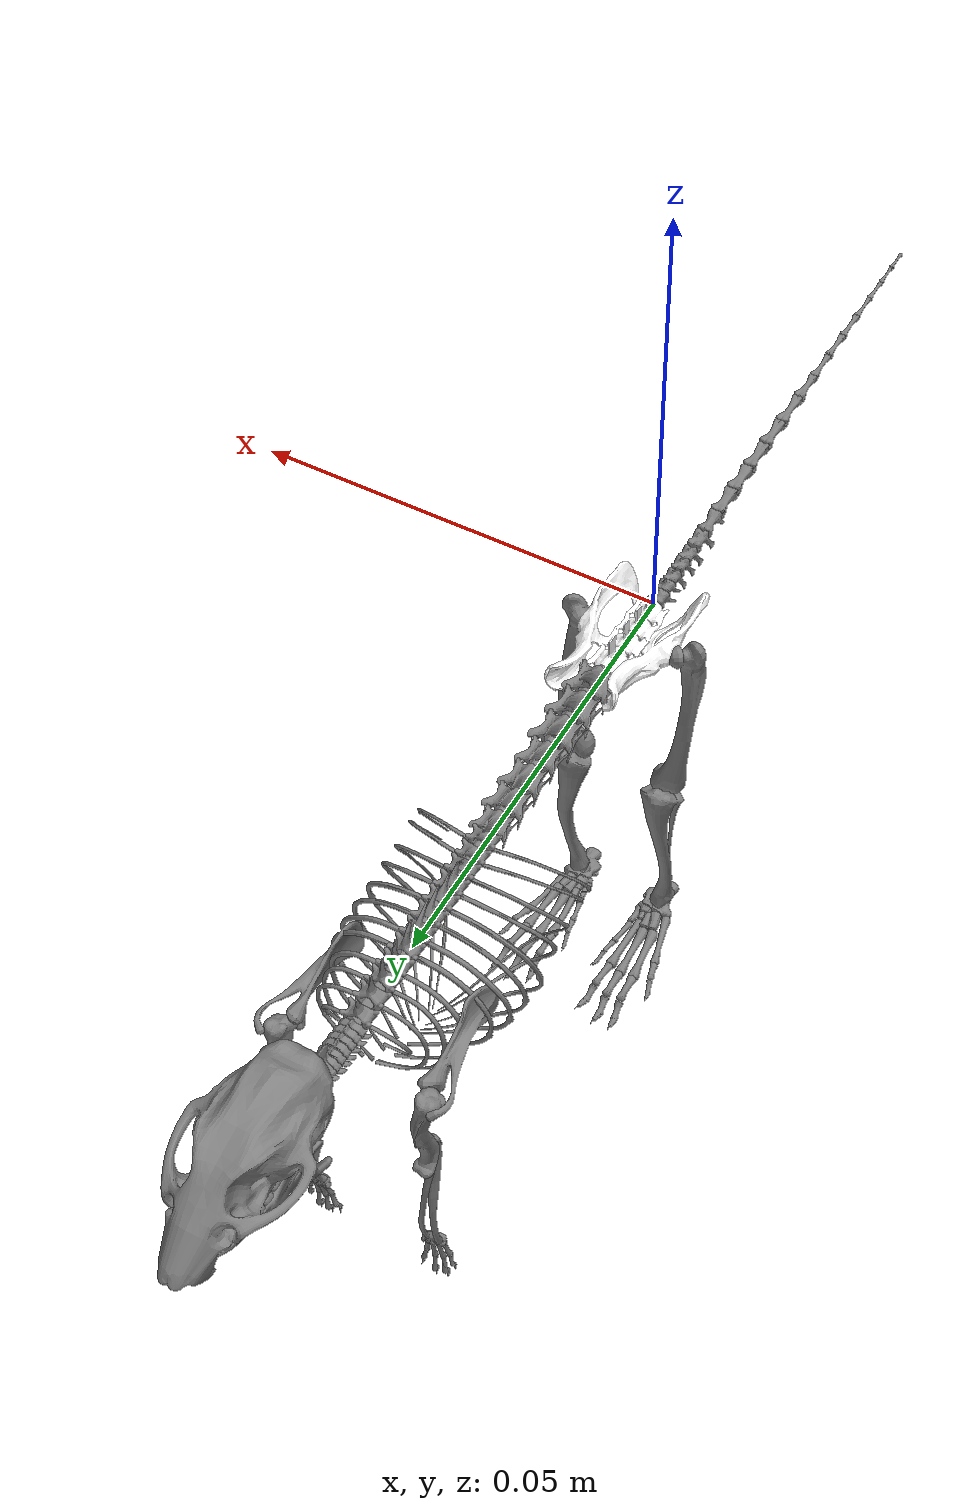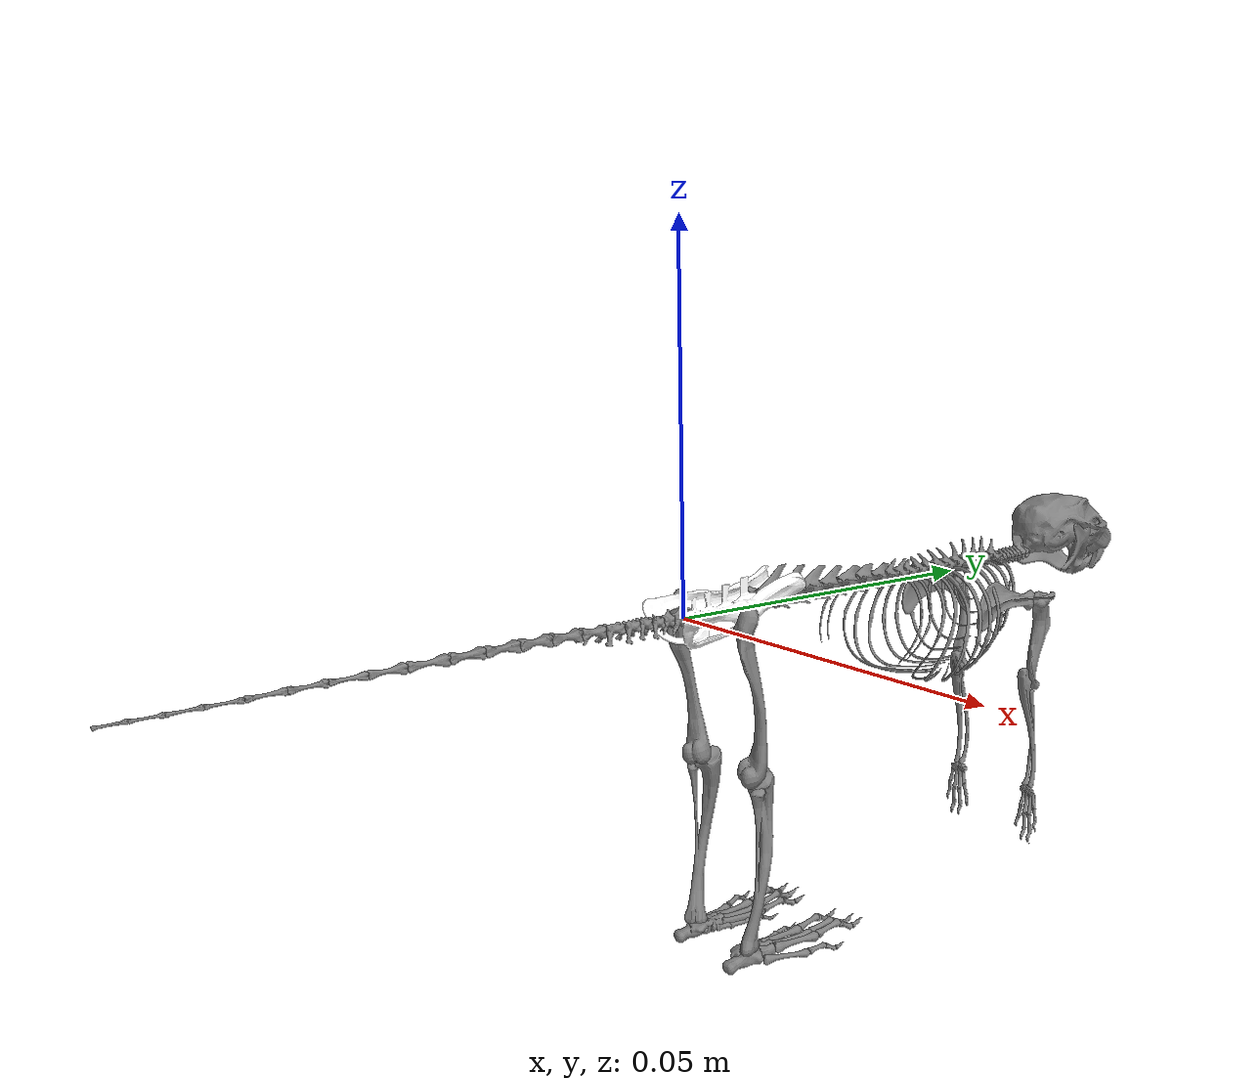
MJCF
<mujoco model="mouse">
    <compiler angle="radian" meshdir="/Users/sungwookmin30/Desktop/Salk VNL/Mouse Data/meshes/stl/"/>
    <option>
        <flag contact="disable"/>
    </option>
    <size njmax="500" nconmax="100"/>
    <visual>
        <global fovy="30" elevation="0" azimuth="0"/>
    </visual>
    <asset>
        <mesh name="Pelvis" file="Pelvis.stl"/>
        <mesh name="Head" file="Head.stl"/>
        <mesh name="Cervical1" file="Cervical1.stl"/>
        <mesh name="Cervical2" file="Cervical2.stl"/>
        <mesh name="Cervical3" file="Cervical3.stl"/>
        <mesh name="Cervical4" file="Cervical4.stl"/>
        <mesh name="Cervical5" file="Cervical5.stl"/>
        <mesh name="Cervical6" file="Cervical6.stl"/>
        <mesh name="Cervical7" file="Cervical7.stl"/>
        <mesh name="Cervical8" file="Cervical8.stl"/>
        <mesh name="Thoracic1" file="Thoracic1.stl"/>
        <mesh name="Thoracic10" file="Thoracic10.stl"/>
        <mesh name="Thoracic11" file="Thoracic11.stl"/>
        <mesh name="Thoracic12" file="Thoracic12.stl"/>
        <mesh name="Thoracic13" file="Thoracic13.stl"/>
        <mesh name="Thoracic2" file="Thoracic2.stl"/>
        <mesh name="Thoracic3" file="Thoracic3.stl"/>
        <mesh name="Thoracic4" file="Thoracic4.stl"/>
        <mesh name="Thoracic5" file="Thoracic5.stl"/>
        <mesh name="Thoracic6" file="Thoracic6.stl"/>
        <mesh name="Thoracic7" file="Thoracic7.stl"/>
        <mesh name="Thoracic8" file="Thoracic8.stl"/>
        <mesh name="Thoracic9" file="Thoracic9.stl"/>
        <mesh name="Lumbar1" file="Lumbar1.stl"/>
        <mesh name="Lumbar2" file="Lumbar2.stl"/>
        <mesh name="Lumbar3" file="Lumbar3.stl"/>
        <mesh name="Lumbar4" file="Lumbar4.stl"/>
        <mesh name="Lumbar5" file="Lumbar5.stl"/>
        <mesh name="Lumbar6" file="Lumbar6.stl"/>
        <mesh name="LFemur" file="LFemur.stl"/>
        <mesh name="LTibia" file="LTibia.stl"/>
        <mesh name="LTarsus" file="LTarsus.stl"/>
        <mesh name="LMetatarsus1" file="LMetatarsus1.stl"/>
        <mesh name="LMetatarsus2" file="LMetatarsus2.stl"/>
        <mesh name="LMetatarsus3" file="LMetatarsus3.stl"/>
        <mesh name="LMetatarsus4" file="LMetatarsus4.stl"/>
        <mesh name="LMetatarsus5" file="LMetatarsus5.stl"/>
        <mesh name="LBPhalange1" file="LBPhalange1.stl"/>
        <mesh name="LBPhalange2" file="LBPhalange2.stl"/>
        <mesh name="LBPhalange3" file="LBPhalange3.stl"/>
        <mesh name="LBPhalange4" file="LBPhalange4.stl"/>
        <mesh name="LBPhalange5" file="LBPhalange5.stl"/>
        <mesh name="RFemur" file="RFemur.stl"/>
        <mesh name="RTibia" file="RTibia.stl"/>
        <mesh name="RTarsus" file="RTarsus.stl"/>
        <mesh name="RMetatarsus1" file="RMetatarsus1.stl"/>
        <mesh name="RMetatarsus2" file="RMetatarsus2.stl"/>
        <mesh name="RMetatarsus3" file="RMetatarsus3.stl"/>
        <mesh name="RMetatarsus4" file="RMetatarsus4.stl"/>
        <mesh name="RMetatarsus5" file="RMetatarsus5.stl"/>
        <mesh name="RBPhalange1" file="RBPhalange1.stl"/>
        <mesh name="RBPhalange2" file="RBPhalange2.stl"/>
        <mesh name="RBPhalange3" file="RBPhalange3.stl"/>
        <mesh name="RBPhalange4" file="RBPhalange4.stl"/>
        <mesh name="RBPhalange5" file="RBPhalange5.stl"/>
        <mesh name="LScapula" file="LScapula.stl"/>
        <mesh name="LHumerus" file="LHumerus.stl"/>
        <mesh name="LUlna" file="LUlna.stl"/>
        <mesh name="LRadius" file="LRadius.stl"/>
        <mesh name="LCarpus" file="LCarpus.stl"/>
        <mesh name="LMetaCarpus1" file="LMetaCarpus1.stl"/>
        <mesh name="LMetaCarpus2" file="LMetaCarpus2.stl"/>
        <mesh name="LMetaCarpus3" file="LMetaCarpus3.stl"/>
        <mesh name="LMetaCarpus4" file="LMetaCarpus4.stl"/>
        <mesh name="LFPhalange1" file="LFPhalange1.stl"/>
        <mesh name="LFPhalange2" file="LFPhalange2.stl"/>
        <mesh name="LFPhalange3" file="LFPhalange3.stl"/>
        <mesh name="LFPhalange4" file="LFPhalange4.stl"/>
        <mesh name="RScapula" file="RScapula.stl"/>
        <mesh name="RHumerus" file="RHumerus.stl"/>
        <mesh name="RUlna" file="RUlna.stl"/>
        <mesh name="RRadius" file="RRadius.stl"/>
        <mesh name="RCarpus" file="RCarpus.stl"/>
        <mesh name="RMetaCarpus1" file="RMetaCarpus1.stl"/>
        <mesh name="RMetaCarpus2" file="RMetaCarpus2.stl"/>
        <mesh name="RMetaCarpus3" file="RMetaCarpus3.stl"/>
        <mesh name="RMetaCarpus4" file="RMetaCarpus4.stl"/>
        <mesh name="RFPhalange1" file="RFPhalange1.stl"/>
        <mesh name="RFPhalange2" file="RFPhalange2.stl"/>
        <mesh name="RFPhalange3" file="RFPhalange3.stl"/>
        <mesh name="RFPhalange4" file="RFPhalange4.stl"/>
        <mesh name="Tail1" file="Tail1.stl"/>
        <mesh name="Tail10" file="Tail10.stl"/>
        <mesh name="Tail11" file="Tail11.stl"/>
        <mesh name="Tail12" file="Tail12.stl"/>
        <mesh name="Tail13" file="Tail13.stl"/>
        <mesh name="Tail14" file="Tail14.stl"/>
        <mesh name="Tail15" file="Tail15.stl"/>
        <mesh name="Tail16" file="Tail16.stl"/>
        <mesh name="Tail17" file="Tail17.stl"/>
        <mesh name="Tail18" file="Tail18.stl"/>
        <mesh name="Tail19" file="Tail19.stl"/>
        <mesh name="Tail2" file="Tail2.stl"/>
        <mesh name="Tail20" file="Tail20.stl"/>
        <mesh name="Tail3" file="Tail3.stl"/>
        <mesh name="Tail4" file="Tail4.stl"/>
        <mesh name="Tail5" file="Tail5.stl"/>
        <mesh name="Tail6" file="Tail6.stl"/>
        <mesh name="Tail7" file="Tail7.stl"/>
        <mesh name="Tail8" file="Tail8.stl"/>
        <mesh name="Tail9" file="Tail9.stl"/>
    </asset>
    <worldbody>
        <geom type="mesh" mesh="Pelvis" rgba="1 1 1 1" />
        <body name="mouse__Lumbar6_interim_0" pos="0 0.01206 0.00074">
            <inertial pos="0 0 0" quat="0.707107 0 0 0.707107" mass="0.000163962" diaginertia="1e-06 1e-06 1e-06"/>
            <joint name="mouse__Lumbar6_bending" pos="0 0 0" axis="0 0 1" limited="true" range="-3.14159 3.14159"/>
            <body name="mouse__Lumbar6_interim_1" pos="0 0 0">
                <inertial pos="0 0 0" quat="0.707107 0 0 0.707107" mass="0.000163962" diaginertia="1e-06 1e-06 1e-06"/>
                <joint name="mouse__Lumbar6_rotation" pos="0 0 0" axis="0 1 0" limited="true" range="-3.14159 3.14159"/>
                <body name="mouse__Lumbar6" pos="0 0 0">
                    <inertial pos="0 0.00252 0.00133" quat="0.707107 0 0 0.707107" mass="0.000163962" diaginertia="1e-06 1e-06 1e-06"/>
                    <joint name="mouse__Lumbar6_flexion" pos="0 0 0" axis="1 0 0" limited="true" range="-3.14159 3.14159"/>
                    <geom type="mesh" mesh="Lumbar6"/>
                    <body name="mouse__Lumbar5_interim_0" pos="0 0.00372 -3e-05">
                        <inertial pos="0 0 0" quat="0.707107 0 0 0.707107" mass="0.000163962" diaginertia="1e-06 1e-06 1e-06"/>
                        <joint name="mouse__Lumbar5_bending" pos="0 0 0" axis="0 0 1" limited="true" range="-3.14159 3.14159"/>
                        <body name="mouse__Lumbar5_interim_1" pos="0 0 0">
                            <inertial pos="0 0 0" quat="0.707107 0 0 0.707107" mass="0.000163962" diaginertia="1e-06 1e-06 1e-06"/>
                            <joint name="mouse__Lumbar5_rotation" pos="0 0 0" axis="0 1 0" limited="true" range="-3.14159 3.14159"/>
                            <body name="mouse__Lumbar5" pos="0 0 0">
                                <inertial pos="0 0.00237 0.00115" quat="0.707107 0 0 0.707107" mass="0.000137716" diaginertia="1e-06 1e-06 1e-06"/>
                                <joint name="mouse__Lumbar5_flexion" pos="0 0 0" axis="1 0 0" limited="true" range="-3.14159 3.14159"/>
                                <geom type="mesh" mesh="Lumbar5"/>
                                <body name="mouse__Lumbar4_interim_0" pos="0 0.00373 -2e-05">
                                    <inertial pos="0 0 0" quat="0.707107 0 0 0.707107" mass="0.000163962" diaginertia="1e-06 1e-06 1e-06"/>
                                    <joint name="mouse__Lumbar4_bending" pos="0 0 0" axis="0 0 1" limited="true" range="-3.14159 3.14159"/>
                                    <body name="mouse__Lumbar4_interim_1" pos="0 0 0">
                                        <inertial pos="0 0 0" quat="0.707107 0 0 0.707107" mass="0.000163962" diaginertia="1e-06 1e-06 1e-06"/>
                                        <joint name="mouse__Lumbar4_rotation" pos="0 0 0" axis="0 1 0" limited="true" range="-3.14159 3.14159"/>
                                        <body name="mouse__Lumbar4" pos="0 0 0">
                                            <inertial pos="0 0.00244 0.00102" quat="0 0.707107 0 0.707107" mass="0.000120721" diaginertia="1e-06 1e-06 1e-06"/>
                                            <joint name="mouse__Lumbar4_flexion" pos="0 0 0" axis="1 0 0" limited="true" range="-3.14159 3.14159"/>
                                            <geom type="mesh" mesh="Lumbar4"/>
                                            <body name="mouse__Lumbar3_interim_0" pos="0 0.00367 1e-05">
                                                <inertial pos="0 0 0" quat="0.707107 0 0 0.707107" mass="0.000163962" diaginertia="1e-06 1e-06 1e-06"/>
                                                <joint name="mouse__Lumbar3_bending" pos="0 0 0" axis="0 0 1" limited="true" range="-3.14159 3.14159"/>
                                                <body name="mouse__Lumbar3_interim_1" pos="0 0 0">
                                                    <inertial pos="0 0 0" quat="0.707107 0 0 0.707107" mass="0.000163962" diaginertia="1e-06 1e-06 1e-06"/>
                                                    <joint name="mouse__Lumbar3_rotation" pos="0 0 0" axis="0 1 0" limited="true" range="-3.14159 3.14159"/>
                                                    <body name="mouse__Lumbar3" pos="0 0 0">
                                                        <inertial pos="0 0.00215 0.00076" quat="0 0.707107 0 0.707107" mass="8.5376e-05" diaginertia="1e-06 1e-06 1e-06"/>
                                                        <joint name="mouse__Lumbar3_flexion" pos="0 0 0" axis="1 0 0" limited="true" range="-3.14159 3.14159"/>
                                                        <geom type="mesh" mesh="Lumbar3"/>
                                                        <body name="mouse__Lumbar2_interim_0" pos="0 0.00329 0">
                                                            <inertial pos="0 0 0" quat="0.707107 0 0 0.707107" mass="0.000163962" diaginertia="1e-06 1e-06 1e-06"/>
                                                            <joint name="mouse__Lumbar2_bending" pos="0 0 0" axis="0 0 1" limited="true" range="-3.14159 3.14159"/>
                                                            <body name="mouse__Lumbar2_interim_1" pos="0 0 0">
                                                                <inertial pos="0 0 0" quat="0.707107 0 0 0.707107" mass="0.000163962" diaginertia="1e-06 1e-06 1e-06"/>
                                                                <joint name="mouse__Lumbar2_rotation" pos="0 0 0" axis="0 1 0" limited="true" range="-3.14159 3.14159"/>
                                                                <body name="mouse__Lumbar2" pos="0 0 0">
                                                                    <inertial pos="0 0.00237 0.00068" quat="0.5 0.5 -0.5 0.5" mass="8.17254e-05" diaginertia="1e-06 1e-06 1e-06"/>
                                                                    <joint name="mouse__Lumbar2_flexion" pos="0 0 0" axis="1 0 0" limited="true" range="-3.14159 3.14159"/>
                                                                    <geom type="mesh" mesh="Lumbar2"/>
                                                                    <body name="mouse__Lumbar1_interim_0" pos="0 0.00334 -2e-05">
                                                                        <inertial pos="0 0 0" quat="0.707107 0 0 0.707107" mass="0.000163962" diaginertia="1e-06 1e-06 1e-06"/>
                                                                        <joint name="mouse__Lumbar1_bending" pos="0 0 0" axis="0 0 1" limited="true" range="-3.14159 3.14159"/>
                                                                        <body name="mouse__Lumbar1_interim_1" pos="0 0 0">
                                                                            <inertial pos="0 0 0" quat="0.707107 0 0 0.707107" mass="0.000163962" diaginertia="1e-06 1e-06 1e-06"/>
                                                                            <joint name="mouse__Lumbar1_rotation" pos="0 0 0" axis="0 1 0" limited="true" range="-3.14159 3.14159"/>
                                                                            <body name="mouse__Lumbar1" pos="0 0 0">
                                                                                <inertial pos="0 0.00185 0.00061" quat="0 0.707107 0 0.707107" mass="6.09118e-05" diaginertia="1e-06 1e-06 1e-06"/>
                                                                                <joint name="mouse__Lumbar1_flexion" pos="0 0 0" axis="1 0 0" limited="true" range="-3.14159 3.14159"/>
                                                                                <geom type="mesh" mesh="Lumbar1"/>
                                                                                <body name="mouse__Thoracic13_interim_0" pos="0 0.00313 0">
                                                                                    <inertial pos="0 0 0" mass="1e-06" diaginertia="1e-06 1e-06 1e-06"/>
                                                                                    <joint name="mouse__Thoracic13_bending" pos="0 0 0" axis="0 0 1" limited="true" range="-3.14159 3.14159"/>
                                                                                    <body name="mouse__Thoracic13_interim_1" pos="0 0 0">
                                                                                        <inertial pos="0 0 0" mass="1e-06" diaginertia="1e-06 1e-06 1e-06"/>
                                                                                        <joint name="mouse__Thoracic13_rotation" pos="0 0 0" axis="0 1 0" limited="true" range="-3.14159 3.14159"/>
                                                                                        <body name="mouse__Thoracic13" pos="0 0 0">
                                                                                            <inertial pos="0 0.00194 0.00048" quat="0 0.707107 0 0.707107" mass="5.4685e-05" diaginertia="1e-06 1e-06 1e-06"/>
                                                                                            <joint name="mouse__Thoracic13_flexion" pos="0 0 0" axis="1 0 0" limited="true" range="-3.14159 3.14159"/>
                                                                                            <geom type="mesh" mesh="Thoracic13"/>
                                                                                            <body name="mouse__Thoracic12_interim_0" pos="0 0.00264 0">
                                                                                                <inertial pos="0 0 0" mass="1e-06" diaginertia="1e-06 1e-06 1e-06"/>
                                                                                                <joint name="mouse__Thoracic12_bending" pos="0 0 0" axis="0 0 1" limited="true" range="-3.14159 3.14159"/>
                                                                                                <body name="mouse__Thoracic12_interim_1" pos="0 0 0">
                                                                                                    <inertial pos="0 0 0" mass="1e-06" diaginertia="1e-06 1e-06 1e-06"/>
                                                                                                    <joint name="mouse__Thoracic12_rotation" pos="0 0 0" axis="0 1 0" limited="true" range="-3.14159 3.14159"/>
                                                                                                    <body name="mouse__Thoracic12" pos="0 0 0">
                                                                                                        <inertial pos="0 -0.00096 -0.00395" quat="0.5 0.5 0.5 0.5" mass="0.00187536" diaginertia="1e-06 1e-06 1e-06"/>
                                                                                                        <joint name="mouse__Thoracic12_flexion" pos="0 0 0" axis="1 0 0" limited="true" range="-3.14159 3.14159"/>
                                                                                                        <geom type="mesh" mesh="Thoracic12"/>
                                                                                                        <body name="mouse__Thoracic11_interim_0" pos="0 0.00198 -2e-05">
                                                                                                            <inertial pos="0 0 0" mass="1e-06" diaginertia="1e-06 1e-06 1e-06"/>
                                                                                                            <joint name="mouse__Thoracic11_bending" pos="0 0 0" axis="0 0 1" limited="true" range="-3.14159 3.14159"/>
                                                                                                            <body name="mouse__Thoracic11_interim_1" pos="0 0 0">
                                                                                                                <inertial pos="0 0 0" mass="1e-06" diaginertia="1e-06 1e-06 1e-06"/>
                                                                                                                <joint name="mouse__Thoracic11_rotation" pos="0 0 0" axis="0 1 0" limited="true" range="-3.14159 3.14159"/>
                                                                                                                <body name="mouse__Thoracic11" pos="0 0 0">
                                                                                                                    <inertial pos="0 -0.00117 -0.00389" quat="0.5 0.5 0.5 0.5" mass="0.00198397" diaginertia="1e-06 1e-06 1e-06"/>
                                                                                                                    <joint name="mouse__Thoracic11_flexion" pos="0 0 0" axis="1 0 0" limited="true" range="-3.14159 3.14159"/>
                                                                                                                    <geom type="mesh" mesh="Thoracic11"/>
                                                                                                                    <body name="mouse__Thoracic10_interim_0" pos="0 0.00199 -2e-05">
                                                                                                                        <inertial pos="0 0 0" mass="1e-06" diaginertia="1e-06 1e-06 1e-06"/>
                                                                                                                        <joint name="mouse__Thoracic10_bending" pos="0 0 0" axis="0 0 1" limited="true" range="-3.14159 3.14159"/>
                                                                                                                        <body name="mouse__Thoracic10_interim_1" pos="0 0 0">
                                                                                                                            <inertial pos="0 0 0" mass="1e-06" diaginertia="1e-06 1e-06 1e-06"/>
                                                                                                                            <joint name="mouse__Thoracic10_rotation" pos="0 0 0" axis="0 1 0" limited="true" range="-3.14159 3.14159"/>
                                                                                                                            <body name="mouse__Thoracic10" pos="0 0 0">
                                                                                                                                <inertial pos="0 0.00214 -0.00697" quat="0.5 0.5 0.5 0.5" mass="0.00422641" diaginertia="1e-06 1e-06 1e-06"/>
                                                                                                                                <joint name="mouse__Thoracic10_flexion" pos="0 0 0" axis="1 0 0" limited="true" range="-3.14159 3.14159"/>
                                                                                                                                <geom type="mesh" mesh="Thoracic10"/>
                                                                                                                                <body name="mouse__Thoracic9_interim_0" pos="0 0.00206 -1e-05">
                                                                                                                                    <inertial pos="0 0 0" mass="1e-06" diaginertia="1e-06 1e-06 1e-06"/>
                                                                                                                                    <joint name="mouse__Thoracic9_bending" pos="0 0 0" axis="0 0 1" limited="true" range="-3.14159 3.14159"/>
                                                                                                                                    <body name="mouse__Thoracic9_interim_1" pos="0 0 0">
                                                                                                                                        <inertial pos="0 0 0" mass="1e-06" diaginertia="1e-06 1e-06 1e-06"/>
                                                                                                                                        <joint name="mouse__Thoracic9_rotation" pos="0 0 0" axis="0 1 0" limited="true" range="-3.14159 3.14159"/>
                                                                                                                                        <body name="mouse__Thoracic9" pos="0 0 0">
                                                                                                                                            <inertial pos="0 0.00162 -0.00669" quat="0.5 0.5 0.5 0.5" mass="0.00365901" diaginertia="1e-06 1e-06 1e-06"/>
                                                                                                                                            <joint name="mouse__Thoracic9_flexion" pos="0 0 0" axis="1 0 0" limited="true" range="-3.14159 3.14159"/>
                                                                                                                                            <geom type="mesh" mesh="Thoracic9"/>
                                                                                                                                            <body name="mouse__Thoracic8_interim_0" pos="0 0.00203 0">
                                                                                                                                                <inertial pos="0 0 0" mass="1e-06" diaginertia="1e-06 1e-06 1e-06"/>
                                                                                                                                                <joint name="mouse__Thoracic8_bending" pos="0 0 0" axis="0 0 1" limited="true" range="-3.14159 3.14159"/>
                                                                                                                                                <body name="mouse__Thoracic8_interim_1" pos="0 0 0">
                                                                                                                                                    <inertial pos="0 0 0" mass="1e-06" diaginertia="1e-06 1e-06 1e-06"/>
                                                                                                                                                    <joint name="mouse__Thoracic8_rotation" pos="0 0 0" axis="0 1 0" limited="true" range="-3.14159 3.14159"/>
                                                                                                                                                    <body name="mouse__Thoracic8" pos="0 0 0">
                                                                                                                                                        <inertial pos="0 0.0021 -0.0064" quat="0.5 0.5 0.5 0.5" mass="0.00302533" diaginertia="1e-06 1e-06 1e-06"/>
                                                                                                                                                        <joint name="mouse__Thoracic8_flexion" pos="0 0 0" axis="1 0 0" limited="true" range="-3.14159 3.14159"/>
                                                                                                                                                        <geom type="mesh" mesh="Thoracic8"/>
                                                                                                                                                        <body name="mouse__Thoracic7_interim_0" pos="0 0.00206 0">
                                                                                                                                                            <inertial pos="0 0 0" mass="1e-06" diaginertia="1e-06 1e-06 1e-06"/>
                                                                                                                                                            <joint name="mouse__Thoracic7_bending" pos="0 0 0" axis="0 0 1" limited="true" range="-3.14159 3.14159"/>
                                                                                                                                                            <body name="mouse__Thoracic7_interim_1" pos="0 0 0">
                                                                                                                                                                <inertial pos="0 0 0" mass="1e-06" diaginertia="1e-06 1e-06 1e-06"/>
                                                                                                                                                                <joint name="mouse__Thoracic7_rotation" pos="0 0 0" axis="0 1 0" limited="true" range="-3.14159 3.14159"/>
                                                                                                                                                                <body name="mouse__Thoracic7" pos="0 0 0">
                                                                                                                                                                    <inertial pos="0 0.00201 -0.00613" quat="0.5 0.5 0.5 0.5" mass="0.00221615" diaginertia="1e-06 1e-06 1e-06"/>
                                                                                                                                                                    <joint name="mouse__Thoracic7_flexion" pos="0 0 0" axis="1 0 0" limited="true" range="-3.14159 3.14159"/>
                                                                                                                                                                    <geom type="mesh" mesh="Thoracic7"/>
                                                                                                                                                                    <body name="mouse__Thoracic6_interim_0" pos="0 0.00205 0">
                                                                                                                                                                        <inertial pos="0 0 0" mass="1e-06" diaginertia="1e-06 1e-06 1e-06"/>
                                                                                                                                                                        <joint name="mouse__Thoracic6_bending" pos="0 0 0" axis="0 0 1" limited="true" range="-3.14159 3.14159"/>
                                                                                                                                                                        <body name="mouse__Thoracic6_interim_1" pos="0 0 0">
                                                                                                                                                                            <inertial pos="0 0 0" mass="1e-06" diaginertia="1e-06 1e-06 1e-06"/>
                                                                                                                                                                            <joint name="mouse__Thoracic6_rotation" pos="0 0 0" axis="0 1 0" limited="true" range="-3.14159 3.14159"/>
                                                                                                                                                                            <body name="mouse__Thoracic6" pos="0 0 0">
                                                                                                                                                                                <inertial pos="0 0.00125 -0.00592" quat="0.5 0.5 0.5 0.5" mass="0.00169488" diaginertia="1e-06 1e-06 1e-06"/>
                                                                                                                                                                                <joint name="mouse__Thoracic6_flexion" pos="0 0 0" axis="1 0 0" limited="true" range="-3.14159 3.14159"/>
                                                                                                                                                                                <geom type="mesh" mesh="Thoracic6"/>
                                                                                                                                                                                <body name="mouse__Thoracic5_interim_0" pos="0 0.00206 0">
                                                                                                                                                                                    <inertial pos="0 0 0" mass="1e-06" diaginertia="1e-06 1e-06 1e-06"/>
                                                                                                                                                                                    <joint name="mouse__Thoracic5_bending" pos="0 0 0" axis="0 0 1" limited="true" range="-3.14159 3.14159"/>
                                                                                                                                                                                    <body name="mouse__Thoracic5_interim_1" pos="0 0 0">
                                                                                                                                                                                        <inertial pos="0 0 0" mass="1e-06" diaginertia="1e-06 1e-06 1e-06"/>
                                                                                                                                                                                        <joint name="mouse__Thoracic5_rotation" pos="0 0 0" axis="0 1 0" limited="true" range="-3.14159 3.14159"/>
                                                                                                                                                                                        <body name="mouse__Thoracic5" pos="0 0 0">
                                                                                                                                                                                            <inertial pos="0 0.00171 -0.00514" quat="0.5 0.5 0.5 0.5" mass="0.00123608" diaginertia="1e-06 1e-06 1e-06"/>
                                                                                                                                                                                            <joint name="mouse__Thoracic5_flexion" pos="0 0 0" axis="1 0 0" limited="true" range="-3.14159 3.14159"/>
                                                                                                                                                                                            <geom type="mesh" mesh="Thoracic5"/>
                                                                                                                                                                                            <body name="mouse__Thoracic4_interim_0" pos="0 0.00203 0">
                                                                                                                                                                                                <inertial pos="0 0 0" mass="1e-06" diaginertia="1e-06 1e-06 1e-06"/>
                                                                                                                                                                                                <joint name="mouse__Thoracic4_bending" pos="0 0 0" axis="0 0 1" limited="true" range="-3.14159 3.14159"/>
                                                                                                                                                                                                <body name="mouse__Thoracic4_interim_1" pos="0 0 0">
                                                                                                                                                                                                    <inertial pos="0 0 0" mass="1e-06" diaginertia="1e-06 1e-06 1e-06"/>
                                                                                                                                                                                                    <joint name="mouse__Thoracic4_rotation" pos="0 0 0" axis="0 1 0" limited="true" range="-3.14159 3.14159"/>
                                                                                                                                                                                                    <body name="mouse__Thoracic4" pos="0 0 0">
                                                                                                                                                                                                        <inertial pos="0 0.00195 -0.00438" quat="0.707107 0 0 0.707107" mass="0.000979661" diaginertia="1e-06 1e-06 1e-06"/>
                                                                                                                                                                                                        <joint name="mouse__Thoracic4_flexion" pos="0 0 0" axis="1 0 0" limited="true" range="-3.14159 3.14159"/>
                                                                                                                                                                                                        <geom type="mesh" mesh="Thoracic4"/>
                                                                                                                                                                                                        <body name="mouse__Thoracic3_interim_0" pos="0 0.00206 1e-05">
                                                                                                                                                                                                            <inertial pos="0 0 0" mass="1e-06" diaginertia="1e-06 1e-06 1e-06"/>
                                                                                                                                                                                                            <joint name="mouse__Thoracic3_bending" pos="0 0 0" axis="0 0 1" limited="true" range="-3.14159 3.14159"/>
                                                                                                                                                                                                            <body name="mouse__Thoracic3_interim_1" pos="0 0 0">
                                                                                                                                                                                                                <inertial pos="0 0 0" mass="1e-06" diaginertia="1e-06 1e-06 1e-06"/>
                                                                                                                                                                                                                <joint name="mouse__Thoracic3_rotation" pos="0 0 0" axis="0 1 0" limited="true" range="-3.14159 3.14159"/>
                                                                                                                                                                                                                <body name="mouse__Thoracic3" pos="0 0 0">
                                                                                                                                                                                                                    <inertial pos="0 0.0021 -0.00342" quat="0.707107 0 0 0.707107" mass="0.000820796" diaginertia="1e-06 1e-06 1e-06"/>
                                                                                                                                                                                                                    <joint name="mouse__Thoracic3_flexion" pos="0 0 0" axis="1 0 0" limited="true" range="-3.14159 3.14159"/>
                                                                                                                                                                                                                    <geom type="mesh" mesh="Thoracic3"/>
                                                                                                                                                                                                                    <body name="mouse__Thoracic2_interim_0" pos="0 0.00198 3e-05">
                                                                                                                                                                                                                        <inertial pos="0 0 0" mass="1e-06" diaginertia="1e-06 1e-06 1e-06"/>
                                                                                                                                                                                                                        <joint name="mouse__Thoracic2_bending" pos="0 0 0" axis="0 0 1" limited="true" range="-3.14159 3.14159"/>
                                                                                                                                                                                                                        <body name="mouse__Thoracic2_interim_1" pos="0 0 0">
                                                                                                                                                                                                                            <inertial pos="0 0 0" mass="1e-06" diaginertia="1e-06 1e-06 1e-06"/>
                                                                                                                                                                                                                            <joint name="mouse__Thoracic2_rotation" pos="0 0 0" axis="0 1 0" limited="true" range="-3.14159 3.14159"/>
                                                                                                                                                                                                                            <body name="mouse__Thoracic2" pos="0 0 0">
                                                                                                                                                                                                                                <inertial pos="0 0.00146 -0.00253" quat="0.707107 0 0 0.707107" mass="0.000449683" diaginertia="1e-06 1e-06 1e-06"/>
                                                                                                                                                                                                                                <joint name="mouse__Thoracic2_flexion" pos="0 0 0" axis="1 0 0" limited="true" range="-3.14159 3.14159"/>
                                                                                                                                                                                                                                <geom type="mesh" mesh="Thoracic2"/>
                                                                                                                                                                                                                                <body name="mouse__Thoracic1_interim_0" pos="0 0.00195 4e-05">
                                                                                                                                                                                                                                    <inertial pos="0 0 0" mass="1e-06" diaginertia="1e-06 1e-06 1e-06"/>
                                                                                                                                                                                                                                    <joint name="mouse__Thoracic1_bending" pos="0 0 0" axis="0 0 1" limited="true" range="-3.14159 3.14159"/>
                                                                                                                                                                                                                                    <body name="mouse__Thoracic1_interim_1" pos="0 0 0">
                                                                                                                                                                                                                                        <inertial pos="0 0 0" mass="1e-06" diaginertia="1e-06 1e-06 1e-06"/>
                                                                                                                                                                                                                                        <joint name="mouse__Thoracic1_rotation" pos="0 0 0" axis="0 1 0" limited="true" range="-3.14159 3.14159"/>
                                                                                                                                                                                                                                        <body name="mouse__Thoracic1" pos="0 0 0">
                                                                                                                                                                                                                                            <inertial pos="0 0.00073 -0.00175" quat="0.707107 0 0 0.707107" mass="0.000247848" diaginertia="1e-06 1e-06 1e-06"/>
                                                                                                                                                                                                                                            <joint name="mouse__Thoracic1_flexion" pos="0 0 0" axis="1 0 0" limited="true" range="-3.14159 3.14159"/>
                                                                                                                                                                                                                                            <geom type="mesh" mesh="Thoracic1"/>
                                                                                                                                                                                                                                            <body name="mouse__Cervical8_interim_0" pos="0 0.00199 4e-05">
                                                                                                                                                                                                                                                <inertial pos="0 0 0" mass="1e-06" diaginertia="1e-06 1e-06 1e-06"/>
                                                                                                                                                                                                                                                <joint name="mouse__Cervical8_bending" pos="0 0 0" axis="0 0 1" limited="true" range="-3.14159 3.14159"/>
                                                                                                                                                                                                                                                <body name="mouse__Cervical8_interim_1" pos="0 0 0">
                                                                                                                                                                                                                                                    <inertial pos="0 0 0" mass="1e-06" diaginertia="1e-06 1e-06 1e-06"/>
                                                                                                                                                                                                                                                    <joint name="mouse__Cervical8_rotation" pos="0 0 0" axis="0 1 0" limited="true" range="-3.14159 3.14159"/>
                                                                                                                                                                                                                                                    <body name="mouse__Cervical8" pos="0 0 0">
                                                                                                                                                                                                                                                        <inertial pos="0 0.00042 -5e-05" quat="0.5 0.5 0.5 0.5" mass="8.61405e-06" diaginertia="1e-06 1e-06 1e-06"/>
                                                                                                                                                                                                                                                        <joint name="mouse__Cervical8_flexion" pos="0 0 0" axis="1 0 0" limited="true" range="-3.14159 3.14159"/>
                                                                                                                                                                                                                                                        <geom type="mesh" mesh="Cervical8"/>
                                                                                                                                                                                                                                                        <body name="mouse__Cervical7_interim_0" pos="0 0.00089 1e-05">
                                                                                                                                                                                                                                                            <inertial pos="0 0 0" mass="1e-06" diaginertia="1e-06 1e-06 1e-06"/>
                                                                                                                                                                                                                                                            <joint name="mouse__Cervical7_bending" pos="0 0 0" axis="0 0 1" limited="true" range="-3.14159 3.14159"/>
                                                                                                                                                                                                                                                            <body name="mouse__Cervical7_interim_1" pos="0 0 0">
                                                                                                                                                                                                                                                                <inertial pos="0 0 0" mass="1e-06" diaginertia="1e-06 1e-06 1e-06"/>
                                                                                                                                                                                                                                                                <joint name="mouse__Cervical7_rotation" pos="0 0 0" axis="0 1 0" limited="true" range="-3.14159 3.14159"/>
                                                                                                                                                                                                                                                                <body name="mouse__Cervical7" pos="0 0 0">
                                                                                                                                                                                                                                                                    <inertial pos="0 0.0004 5e-05" quat="0.5 0.5 0.5 0.5" mass="8.42975e-06" diaginertia="1e-06 1e-06 1e-06"/>
                                                                                                                                                                                                                                                                    <joint name="mouse__Cervical7_flexion" pos="0 0 0" axis="1 0 0" limited="true" range="-3.14159 3.14159"/>
                                                                                                                                                                                                                                                                    <geom type="mesh" mesh="Cervical7"/>
                                                                                                                                                                                                                                                                    <body name="mouse__Cervical6_interim_0" pos="0 0.00086 1e-05">
                                                                                                                                                                                                                                                                        <inertial pos="0 0 0" mass="1e-06" diaginertia="1e-06 1e-06 1e-06"/>
                                                                                                                                                                                                                                                                        <joint name="mouse__Cervical6_bending" pos="0 0 0" axis="0 0 1" limited="true" range="-3.14159 3.14159"/>
                                                                                                                                                                                                                                                                        <body name="mouse__Cervical6_interim_1" pos="0 0 0">
                                                                                                                                                                                                                                                                            <inertial pos="0 0 0" mass="1e-06" diaginertia="1e-06 1e-06 1e-06"/>
                                                                                                                                                                                                                                                                            <joint name="mouse__Cervical6_rotation" pos="0 0 0" axis="0 1 0" limited="true" range="-3.14159 3.14159"/>
                                                                                                                                                                                                                                                                            <body name="mouse__Cervical6" pos="0 0 0">
                                                                                                                                                                                                                                                                                <inertial pos="0 0.00039 0.0001" quat="0.5 0.5 0.5 0.5" mass="8.28884e-06" diaginertia="1e-06 1e-06 1e-06"/>
                                                                                                                                                                                                                                                                                <joint name="mouse__Cervical6_flexion" pos="0 0 0" axis="1 0 0" limited="true" range="-3.14159 3.14159"/>
                                                                                                                                                                                                                                                                                <geom type="mesh" mesh="Cervical6"/>
                                                                                                                                                                                                                                                                                <body name="mouse__Cervical5_interim_0" pos="0 0.00083 1e-05">
                                                                                                                                                                                                                                                                                    <inertial pos="0 0 0" mass="1e-06" diaginertia="1e-06 1e-06 1e-06"/>
                                                                                                                                                                                                                                                                                    <joint name="mouse__Cervical5_bending" pos="0 0 0" axis="0 0 1" limited="true" range="-3.14159 3.14159"/>
                                                                                                                                                                                                                                                                                    <body name="mouse__Cervical5_interim_1" pos="0 0 0">
                                                                                                                                                                                                                                                                                        <inertial pos="0 0 0" mass="1e-06" diaginertia="1e-06 1e-06 1e-06"/>
                                                                                                                                                                                                                                                                                        <joint name="mouse__Cervical5_rotation" pos="0 0 0" axis="0 1 0" limited="true" range="-3.14159 3.14159"/>
                                                                                                                                                                                                                                                                                        <body name="mouse__Cervical5" pos="0 0 0">
                                                                                                                                                                                                                                                                                            <inertial pos="0 0.00041 0.00013" quat="0.5 0.5 0.5 0.5" mass="8.21986e-06" diaginertia="1e-06 1e-06 1e-06"/>
                                                                                                                                                                                                                                                                                            <joint name="mouse__Cervical5_flexion" pos="0 0 0" axis="1 0 0" limited="true" range="-3.14159 3.14159"/>
                                                                                                                                                                                                                                                                                            <geom type="mesh" mesh="Cervical5"/>
                                                                                                                                                                                                                                                                                            <body name="mouse__Cervical4_interim_0" pos="0 0.00081 1e-05">
                                                                                                                                                                                                                                                                                                <inertial pos="0 0 0" mass="1e-06" diaginertia="1e-06 1e-06 1e-06"/>
                                                                                                                                                                                                                                                                                                <joint name="mouse__Cervical4_bending" pos="0 0 0" axis="0 0 1" limited="true" range="-3.14159 3.14159"/>
                                                                                                                                                                                                                                                                                                <body name="mouse__Cervical4_interim_1" pos="0 0 0">
                                                                                                                                                                                                                                                                                                    <inertial pos="0 0 0" mass="1e-06" diaginertia="1e-06 1e-06 1e-06"/>
                                                                                                                                                                                                                                                                                                    <joint name="mouse__Cervical4_rotation" pos="0 0 0" axis="0 1 0" limited="true" range="-3.14159 3.14159"/>
                                                                                                                                                                                                                                                                                                    <body name="mouse__Cervical4" pos="0 0 0">
                                                                                                                                                                                                                                                                                                        <inertial pos="0 0.00038 0.00015" quat="0.5 0.5 0.5 0.5" mass="8.56537e-06" diaginertia="1e-06 1e-06 1e-06"/>
                                                                                                                                                                                                                                                                                                        <joint name="mouse__Cervical4_flexion" pos="0 0 0" axis="1 0 0" limited="true" range="-3.14159 3.14159"/>
                                                                                                                                                                                                                                                                                                        <geom type="mesh" mesh="Cervical4"/>
                                                                                                                                                                                                                                                                                                        <body name="mouse__Cervical3_interim_0" pos="0 0.00086 0">
                                                                                                                                                                                                                                                                                                            <inertial pos="0 0 0" mass="1e-06" diaginertia="1e-06 1e-06 1e-06"/>
                                                                                                                                                                                                                                                                                                            <joint name="mouse__Cervical3_bending" pos="0 0 0" axis="0 0 1" limited="true" range="-3.14159 3.14159"/>
                                                                                                                                                                                                                                                                                                            <body name="mouse__Cervical3_interim_1" pos="0 0 0">
                                                                                                                                                                                                                                                                                                                <inertial pos="0 0 0" mass="1e-06" diaginertia="1e-06 1e-06 1e-06"/>
                                                                                                                                                                                                                                                                                                                <joint name="mouse__Cervical3_rotation" pos="0 0 0" axis="0 1 0" limited="true" range="-3.14159 3.14159"/>
                                                                                                                                                                                                                                                                                                                <body name="mouse__Cervical3" pos="0 0 0">
                                                                                                                                                                                                                                                                                                                    <inertial pos="0 0.00033 0.00017" quat="0.5 0.5 0.5 0.5" mass="8.43003e-06" diaginertia="1e-06 1e-06 1e-06"/>
                                                                                                                                                                                                                                                                                                                    <joint name="mouse__Cervical3_flexion" pos="0 0 0" axis="1 0 0" limited="true" range="-3.14159 3.14159"/>
                                                                                                                                                                                                                                                                                                                    <geom type="mesh" mesh="Cervical3"/>
                                                                                                                                                                                                                                                                                                                    <body name="mouse__Cervical2_interim_0" pos="0 0.00081 0">
                                                                                                                                                                                                                                                                                                                        <inertial pos="0 0 0" mass="1e-06" diaginertia="1e-06 1e-06 1e-06"/>
                                                                                                                                                                                                                                                                                                                        <joint name="mouse__Cervical2_bending" pos="0 0 0" axis="0 0 1" limited="true" range="-3.14159 3.14159"/>
                                                                                                                                                                                                                                                                                                                        <body name="mouse__Cervical2_interim_1" pos="0 0 0">
                                                                                                                                                                                                                                                                                                                            <inertial pos="0 0 0" mass="1e-06" diaginertia="1e-06 1e-06 1e-06"/>
                                                                                                                                                                                                                                                                                                                            <joint name="mouse__Cervical2_rotation" pos="0 0 0" axis="0 1 0" limited="true" range="-3.14159 3.14159"/>
                                                                                                                                                                                                                                                                                                                            <body name="mouse__Cervical2" pos="0 0 0">
                                                                                                                                                                                                                                                                                                                                <inertial pos="0 0.00043 0.001" quat="0.707107 0 0 0.707107" mass="3.51285e-05" diaginertia="1e-06 1e-06 1e-06"/>
                                                                                                                                                                                                                                                                                                                                <joint name="mouse__Cervical2_flexion" pos="0 0 0" axis="1 0 0" limited="true" range="-3.14159 3.14159"/>
                                                                                                                                                                                                                                                                                                                                <geom type="mesh" mesh="Cervical2"/>
                                                                                                                                                                                                                                                                                                                                <body name="mouse__Cervical1_interim_0" pos="0 0.00113 2e-05">
                                                                                                                                                                                                                                                                                                                                    <inertial pos="0 0 0" mass="1e-06" diaginertia="1e-06 1e-06 1e-06"/>
                                                                                                                                                                                                                                                                                                                                    <joint name="mouse__Cervical1_bending" pos="0 0 0" axis="0 0 1" limited="true" range="-3.14159 3.14159"/>
                                                                                                                                                                                                                                                                                                                                    <body name="mouse__Cervical1_interim_1" pos="0 0 0">
                                                                                                                                                                                                                                                                                                                                        <inertial pos="0 0 0" mass="1e-06" diaginertia="1e-06 1e-06 1e-06"/>
                                                                                                                                                                                                                                                                                                                                        <joint name="mouse__Cervical1_rotation" pos="0 0 0" axis="0 1 0" limited="true" range="-3.14159 3.14159"/>
                                                                                                                                                                                                                                                                                                                                        <body name="mouse__Cervical1" pos="0 0 0">
                                                                                                                                                                                                                                                                                                                                            <inertial pos="0 0.00036 0.0004" quat="0.5 0.5 0.5 0.5" mass="9.13264e-06" diaginertia="1e-06 1e-06 1e-06"/>
                                                                                                                                                                                                                                                                                                                                            <joint name="mouse__Cervical1_flexion" pos="0 0 0" axis="1 0 0" limited="true" range="-3.14159 3.14159"/>
                                                                                                                                                                                                                                                                                                                                            <geom type="mesh" mesh="Cervical1"/>
                                                                                                                                                                                                                                                                                                                                            <body name="mouse__Head_interim_0" pos="0 0.00085 2e-05">
                                                                                                                                                                                                                                                                                                                                                <inertial pos="0 0 0" mass="1e-06" diaginertia="1e-06 1e-06 1e-06"/>
                                                                                                                                                                                                                                                                                                                                                <joint name="mouse__Head_adduction" pos="0 0 0" axis="0 0 1" limited="true" range="-3.14159 3.14159"/>
                                                                                                                                                                                                                                                                                                                                                <body name="mouse__Head_interim_1" pos="0 0 0">
                                                                                                                                                                                                                                                                                                                                                    <inertial pos="0 0 0" mass="1e-06" diaginertia="1e-06 1e-06 1e-06"/>
                                                                                                                                                                                                                                                                                                                                                    <joint name="mouse__Head_rotation" pos="0 0 0" axis="0 1 0" limited="true" range="-3.14159 3.14159"/>
                                                                                                                                                                                                                                                                                                                                                    <body name="mouse__Head" pos="0 0 0">
                                                                                                                                                                                                                                                                                                                                                        <inertial pos="0 0.01046 0.00191" quat="0.707107 0.707107 0 0" mass="0.00403045" diaginertia="1e-06 1e-06 1e-06"/>
                                                                                                                                                                                                                                                                                                                                                        <joint name="mouse__Head_flexion" pos="0 0 0" axis="1 0 0" limited="true" range="-3.14159 3.14159"/>
                                                                                                                                                                                                                                                                                                                                                        <geom type="mesh" mesh="Head"/>
                                                                                                                                                                                                                                                                                                                                                    </body>
                                                                                                                                                                                                                                                                                                                                                </body>
                                                                                                                                                                                                                                                                                                                                            </body>
                                                                                                                                                                                                                                                                                                                                        </body>
                                                                                                                                                                                                                                                                                                                                    </body>
                                                                                                                                                                                                                                                                                                                                </body>
                                                                                                                                                                                                                                                                                                                            </body>
                                                                                                                                                                                                                                                                                                                        </body>
                                                                                                                                                                                                                                                                                                                    </body>
                                                                                                                                                                                                                                                                                                                </body>
                                                                                                                                                                                                                                                                                                            </body>
                                                                                                                                                                                                                                                                                                        </body>
                                                                                                                                                                                                                                                                                                    </body>
                                                                                                                                                                                                                                                                                                </body>
                                                                                                                                                                                                                                                                                            </body>
                                                                                                                                                                                                                                                                                        </body>
                                                                                                                                                                                                                                                                                    </body>
                                                                                                                                                                                                                                                                                </body>
                                                                                                                                                                                                                                                                            </body>
                                                                                                                                                                                                                                                                        </body>
                                                                                                                                                                                                                                                                    </body>
                                                                                                                                                                                                                                                                </body>
                                                                                                                                                                                                                                                            </body>
                                                                                                                                                                                                                                                        </body>
                                                                                                                                                                                                                                                    </body>
                                                                                                                                                                                                                                                </body>
                                                                                                                                                                                                                                            </body>
                                                                                                                                                                                                                                            <body name="mouse__LScapula" pos="-0.00687 0.00335 -0.00575">
                                                                                                                                                                                                                                                <inertial pos="-0.00162 -0.00587 0.00058" quat="0.707107 0.707107 0 0" mass="0.000444827" diaginertia="1e-06 1e-06 1e-06"/>
                                                                                                                                                                                                                                                <joint name="mouse__LScapula_rotation" pos="0 0 0" axis="0 0 1" limited="true" range="-3.14159 3.14159"/>
                                                                                                                                                                                                                                                <geom type="mesh" mesh="LScapula"/>
                                                                                                                                                                                                                                                <body name="mouse__LHumerus_interim_0" pos="0 0 0">
                                                                                                                                                                                                                                                    <inertial pos="0 0 0" mass="1e-06" diaginertia="1e-06 1e-06 1e-06"/>
                                                                                                                                                                                                                                                    <joint name="mouse__LShoulder_rotation" pos="0 0 0" axis="0 0 1" limited="true" range="-3.14159 3.14159"/>
                                                                                                                                                                                                                                                    <body name="mouse__LHumerus_interim_1" pos="0 0 0">
                                                                                                                                                                                                                                                        <inertial pos="0 0 0" mass="1e-06" diaginertia="1e-06 1e-06 1e-06"/>
                                                                                                                                                                                                                                                        <joint name="mouse__LShoulder_adduction" pos="0 0 0" axis="0 1 0" limited="true" range="-3.14159 3.14159"/>
                                                                                                                                                                                                                                                        <body name="mouse__LHumerus" pos="0 0 0">
                                                                                                                                                                                                                                                            <inertial pos="-0.00091 0.00049 -0.00632" mass="0.000245766" diaginertia="1e-06 1e-06 1e-06"/>
                                                                                                                                                                                                                                                            <joint name="mouse__LShoulder_flexion" pos="0 0 0" axis="1 0 0" limited="true" range="-3.14159 3.14159"/>
                                                                                                                                                                                                                                                            <geom type="mesh" mesh="LHumerus"/>
                                                                                                                                                                                                                                                            <body name="mouse__LUlna" pos="9e-05 0.00015 -0.01337">
                                                                                                                                                                                                                                                                <inertial pos="-0.00027 -0.00079 -0.00691" mass="0.000139187" diaginertia="1e-06 1e-06 1e-06"/>
                                                                                                                                                                                                                                                                <joint name="mouse__LElbow_flexion" pos="0 0 0" axis="1 0 0" limited="true" range="-3.14159 3.14159"/>
                                                                                                                                                                                                                                                                <geom type="mesh" mesh="LUlna"/>
                                                                                                                                                                                                                                                                <body name="mouse__LRadius" pos="-0.0005 0 -0.0009">
                                                                                                                                                                                                                                                                    <inertial pos="0.000255751 0.000285751 -0.00777399" quat="0.999749 -0.0158457 0.0158377 -0.000251023" mass="6.11974e-05" diaginertia="2.00007e-06 2.00007e-06 2e-06"/>
                                                                                                                                                                                                                                                                    <joint name="mouse__LElbow_supination" pos="0 0 0" axis="0 0 1" limited="true" range="-3.14159 3.14159"/>
                                                                                                                                                                                                                                                                    <geom type="mesh" mesh="LRadius"/>
                                                                                                                                                                                                                                                                    <body name="mouse__LCarpus_interim_0" pos="0.00019 0.00051 -0.01488">
                                                                                                                                                                                                                                                                        <inertial pos="0 0 0" mass="1e-06" diaginertia="1e-06 1e-06 1e-06"/>
                                                                                                                                                                                                                                                                        <joint name="mouse__LWrist_adduction" pos="0 0 0" axis="0 1 0" limited="true" range="-3.14159 3.14159"/>
                                                                                                                                                                                                                                                                        <body name="mouse__LCarpus" pos="0 0 0">
                                                                                                                                                                                                                                                                            <inertial pos="0.00014 -0.00066 -0.00119" quat="0.5 0.5 0.5 0.5" mass="5.91924e-06" diaginertia="1e-06 1e-06 1e-06"/>
                                                                                                                                                                                                                                                                            <joint name="mouse__LWrist_flexion" pos="0 0 0" axis="1 0 0" limited="true" range="-3.14159 3.14159"/>
                                                                                                                                                                                                                                                                            <geom type="mesh" mesh="LCarpus"/>
                                                                                                                                                                                                                                                                            <body name="mouse__LMetaCarpus1" pos="-0.00096 0 -0.00153">
                                                                                                                                                                                                                                                                                <inertial pos="-0.00023 -0.00089 -0.00124" quat="0.707107 0 0 0.707107" mass="1.67097e-06" diaginertia="1e-06 1e-06 1e-06"/>
                                                                                                                                                                                                                                                                                <joint name="mouse__LMetaCarpus1_flexion" pos="0 0 0" axis="1 0 0" limited="true" range="-3.14159 3.14159"/>
                                                                                                                                                                                                                                                                                <geom type="mesh" mesh="LMetaCarpus1"/>
                                                                                                                                                                                                                                                                                <body name="mouse__LFPhalange1" pos="-0.00049 6e-05 -0.00207">
                                                                                                                                                                                                                                                                                    <inertial pos="-0.0001 -0.00098 -0.00204" quat="0.707107 0 0 0.707107" mass="2.74249e-06" diaginertia="1e-06 1e-06 1e-06"/>
                                                                                                                                                                                                                                                                                    <joint name="mouse__LFPhalange1_flexion" pos="0 0 0" axis="1 0 0" limited="true" range="-3.14159 3.14159"/>
                                                                                                                                                                                                                                                                                    <geom type="mesh" mesh="LFPhalange1"/>
                                                                                                                                                                                                                                                                                </body>
                                                                                                                                                                                                                                                                            </body>
                                                                                                                                                                                                                                                                            <body name="mouse__LMetaCarpus2" pos="-0.00056 5e-05 -0.0015">
                                                                                                                                                                                                                                                                                <inertial pos="0 -0.00075 -0.00192" mass="2.30115e-06" diaginertia="1e-06 1e-06 1e-06"/>
                                                                                                                                                                                                                                                                                <joint name="mouse__LMetaCarpus2_flexion" pos="0 0 0" axis="1 0 0" limited="true" range="-3.14159 3.14159"/>
                                                                                                                                                                                                                                                                                <geom type="mesh" mesh="LMetaCarpus2"/>
                                                                                                                                                                                                                                                                                <body name="mouse__LFPhalange2" pos="-0.00017 5e-05 -0.00321">
                                                                                                                                                                                                                                                                                    <inertial pos="-4e-05 -0.00078 -0.00278" mass="5.30697e-06" diaginertia="1e-06 1e-06 1e-06"/>
                                                                                                                                                                                                                                                                                    <joint name="mouse__LFPhalange2_flexion" pos="0 0 0" axis="1 0 0" limited="true" range="-3.14159 3.14159"/>
                                                                                                                                                                                                                                                                                    <geom type="mesh" mesh="LFPhalange2"/>
                                                                                                                                                                                                                                                                                </body>
                                                                                                                                                                                                                                                                            </body>
                                                                                                                                                                                                                                                                            <body name="mouse__LMetaCarpus3" pos="3e-05 5e-05 -0.00152">
                                                                                                                                                                                                                                                                                <inertial pos="0.00014 -0.00055 -0.00192" mass="2.25144e-06" diaginertia="1e-06 1e-06 1e-06"/>
                                                                                                                                                                                                                                                                                <joint name="mouse__LMetaCarpus3_flexion" pos="0 0 0" axis="1 0 0" limited="true" range="-3.14159 3.14159"/>
                                                                                                                                                                                                                                                                                <geom type="mesh" mesh="LMetaCarpus3"/>
                                                                                                                                                                                                                                                                                <body name="mouse__LFPhalange3" pos="0.00012 0.00012 -0.00318">
                                                                                                                                                                                                                                                                                    <inertial pos="7e-05 -0.00058 -0.00279" mass="3.88468e-06" diaginertia="1e-06 1e-06 1e-06"/>
                                                                                                                                                                                                                                                                                    <joint name="mouse__LFPhalange3_flexion" pos="0 0 0" axis="1 0 0" limited="true" range="-3.14159 3.14159"/>
                                                                                                                                                                                                                                                                                    <geom type="mesh" mesh="LFPhalange3"/>
                                                                                                                                                                                                                                                                                </body>
                                                                                                                                                                                                                                                                            </body>
                                                                                                                                                                                                                                                                            <body name="mouse__LMetaCarpus4" pos="0.00075 4e-05 -0.00137">
                                                                                                                                                                                                                                                                                <inertial pos="0.00012 -0.00044 -0.00148" quat="0.707107 0 0 0.707107" mass="1.47308e-06" diaginertia="1e-06 1e-06 1e-06"/>
                                                                                                                                                                                                                                                                                <joint name="mouse__LMetaCarpus4_flexion" pos="0 0 0" axis="1 0 0" limited="true" range="-3.14159 3.14159"/>
                                                                                                                                                                                                                                                                                <geom type="mesh" mesh="LMetaCarpus4"/>
                                                                                                                                                                                                                                                                                <body name="mouse__LFPhalange4" pos="0.00021 3e-05 -0.00228">
                                                                                                                                                                                                                                                                                    <inertial pos="0.00033 -0.00032 -0.00238" quat="0.707107 0 0 0.707107" mass="4.51883e-06" diaginertia="1e-06 1e-06 1e-06"/>
                                                                                                                                                                                                                                                                                    <joint name="mouse__LFPhalange4_flexion" pos="0 0 0" axis="1 0 0" limited="true" range="-3.14159 3.14159"/>
                                                                                                                                                                                                                                                                                    <geom type="mesh" mesh="LFPhalange4"/>
                                                                                                                                                                                                                                                                                </body>
                                                                                                                                                                                                                                                                            </body>
                                                                                                                                                                                                                                                                            <body name="mouse__LMetaCarpus5" pos="0.00106 5e-05 -0.0014">
                                                                                                                                                                                                                                                                                <inertial pos="0.00025 -0.00024 -0.00073" quat="0.707107 0 0 0.707107" mass="1e-06" diaginertia="1e-06 1e-06 1e-06"/>
                                                                                                                                                                                                                                                                                <joint name="mouse__LMetaCarpus5_flexion" pos="0 0 0" axis="1 0 0" limited="true" range="-3.14159 3.14159"/>
                                                                                                                                                                                                                                                                                <body name="mouse__LFPhalange5" pos="0.00029 0 -0.00093">
                                                                                                                                                                                                                                                                                    <inertial pos="0.00024 -0.00011 -0.00119" quat="0.707107 0 0 0.707107" mass="1e-06" diaginertia="1e-06 1e-06 1e-06"/>
                                                                                                                                                                                                                                                                                    <joint name="mouse__LFPhalange5_flexion" pos="0 0 0" axis="1 0 0" limited="true" range="-3.14159 3.14159"/>
                                                                                                                                                                                                                                                                                </body>
                                                                                                                                                                                                                                                                            </body>
                                                                                                                                                                                                                                                                        </body>
                                                                                                                                                                                                                                                                    </body>
                                                                                                                                                                                                                                                                </body>
                                                                                                                                                                                                                                                            </body>
                                                                                                                                                                                                                                                        </body>
                                                                                                                                                                                                                                                    </body>
                                                                                                                                                                                                                                                </body>
                                                                                                                                                                                                                                            </body>
                                                                                                                                                                                                                                            <body name="mouse__RScapula" pos="0.00687 0.00335 -0.00575">
                                                                                                                                                                                                                                                <inertial pos="0.00162 -0.00587 0.00058" quat="0.707107 0.707107 0 0" mass="0.000444817" diaginertia="1e-06 1e-06 1e-06"/>
                                                                                                                                                                                                                                                <joint name="mouse__RScapula_rotation" pos="0 0 0" axis="0 0 1" limited="true" range="-3.14159 3.14159"/>
                                                                                                                                                                                                                                                <geom type="mesh" mesh="RScapula"/>
                                                                                                                                                                                                                                                <body name="mouse__RHumerus_interim_0" pos="0 0 0">
                                                                                                                                                                                                                                                    <inertial pos="0 0 0" mass="1e-06" diaginertia="1e-06 1e-06 1e-06"/>
                                                                                                                                                                                                                                                    <joint name="mouse__RShoulder_rotation" pos="0 0 0" axis="0 0 1" limited="true" range="-3.14159 3.14159"/>
                                                                                                                                                                                                                                                    <body name="mouse__RHumerus_interim_1" pos="0 0 0">
                                                                                                                                                                                                                                                        <inertial pos="0 0 0" mass="1e-06" diaginertia="1e-06 1e-06 1e-06"/>
                                                                                                                                                                                                                                                        <joint name="mouse__RShoulder_adduction" pos="0 0 0" axis="0 1 0" limited="true" range="-3.14159 3.14159"/>
                                                                                                                                                                                                                                                        <body name="mouse__RHumerus" pos="0 0 0">
                                                                                                                                                                                                                                                            <inertial pos="0.00091 0.00049 -0.00632" mass="0.000245755" diaginertia="1e-06 1e-06 1e-06"/>
                                                                                                                                                                                                                                                            <joint name="mouse__RShoulder_flexion" pos="0 0 0" axis="1 0 0" limited="true" range="-3.14159 3.14159"/>
                                                                                                                                                                                                                                                            <geom type="mesh" mesh="RHumerus"/>
                                                                                                                                                                                                                                                            <body name="mouse__RUlna" pos="-9e-05 0.00015 -0.01337">
                                                                                                                                                                                                                                                                <inertial pos="0.00026 -0.00079 -0.00691" mass="0.000138974" diaginertia="1e-06 1e-06 1e-06"/>
                                                                                                                                                                                                                                                                <joint name="mouse__RElbow_flexion" pos="0 0 0" axis="1 0 0" limited="true" range="-3.14159 3.14159"/>
                                                                                                                                                                                                                                                                <geom type="mesh" mesh="RUlna"/>
                                                                                                                                                                                                                                                                <body name="mouse__RRadius" pos="0.0005 0 -0.0009">
                                                                                                                                                                                                                                                                    <inertial pos="-0.000255753 0.000285753 -0.00777394" quat="0.999749 -0.0158457 -0.0158377 0.000251023" mass="6.12219e-05" diaginertia="2.00007e-06 2.00007e-06 2e-06"/>
                                                                                                                                                                                                                                                                    <joint name="mouse__RElbow_supination" pos="0 0 0" axis="0 0 1" limited="true" range="-3.14159 3.14159"/>
                                                                                                                                                                                                                                                                    <geom type="mesh" mesh="RRadius"/>
                                                                                                                                                                                                                                                                    <body name="mouse__RCarpus_interim_0" pos="-0.00019 0.00051 -0.01488">
                                                                                                                                                                                                                                                                        <inertial pos="0 0 0" mass="1e-06" diaginertia="1e-06 1e-06 1e-06"/>
                                                                                                                                                                                                                                                                        <joint name="mouse__RWrist_adduction" pos="0 0 0" axis="0 1 0" limited="true" range="-3.14159 3.14159"/>
                                                                                                                                                                                                                                                                        <body name="mouse__RCarpus" pos="0 0 0">
                                                                                                                                                                                                                                                                            <inertial pos="6e-05 -0.00059 -0.00122" quat="0.5 0.5 0.5 0.5" mass="4.6133e-06" diaginertia="1e-06 1e-06 1e-06"/>
                                                                                                                                                                                                                                                                            <joint name="mouse__RWrist_flexion" pos="0 0 0" axis="1 0 0" limited="true" range="-3.14159 3.14159"/>
                                                                                                                                                                                                                                                                            <geom type="mesh" mesh="RCarpus"/>
                                                                                                                                                                                                                                                                            <body name="mouse__RMetaCarpus1" pos="0.00096 0 -0.00153">
                                                                                                                                                                                                                                                                                <inertial pos="0.00045 -0.00061 -0.0013" quat="0.707107 0 0 0.707107" mass="1.67034e-06" diaginertia="1e-06 1e-06 1e-06"/>
                                                                                                                                                                                                                                                                                <joint name="mouse__RMetaCarpus1_flexion" pos="0 0 0" axis="1 0 0" limited="true" range="-3.14159 3.14159"/>
                                                                                                                                                                                                                                                                                <geom type="mesh" mesh="RMetaCarpus1"/>
                                                                                                                                                                                                                                                                                <body name="mouse__RFPhalange1" pos="0.00049 6e-05 -0.00207">
                                                                                                                                                                                                                                                                                    <inertial pos="0.00028 -0.00078 -0.00211" mass="2.69227e-06" diaginertia="1e-06 1e-06 1e-06"/>
                                                                                                                                                                                                                                                                                    <joint name="mouse__RFPhalange1_flexion" pos="0 0 0" axis="1 0 0" limited="true" range="-3.14159 3.14159"/>
                                                                                                                                                                                                                                                                                    <geom type="mesh" mesh="RFPhalange1"/>
                                                                                                                                                                                                                                                                                </body>
                                                                                                                                                                                                                                                                            </body>
                                                                                                                                                                                                                                                                            <body name="mouse__RMetaCarpus2" pos="0.00056 5e-05 -0.0015">
                                                                                                                                                                                                                                                                                <inertial pos="0.00017 -0.00067 -0.00194" mass="2.5519e-06" diaginertia="1e-06 1e-06 1e-06"/>
                                                                                                                                                                                                                                                                                <joint name="mouse__RMetaCarpus2_flexion" pos="0 0 0" axis="1 0 0" limited="true" range="-3.14159 3.14159"/>
                                                                                                                                                                                                                                                                                <geom type="mesh" mesh="RMetaCarpus2"/>
                                                                                                                                                                                                                                                                                <body name="mouse__RFPhalange2" pos="0.00017 5e-05 -0.00321">
                                                                                                                                                                                                                                                                                    <inertial pos="0.00014 -0.00094 -0.00281" mass="4.84528e-06" diaginertia="1e-06 1e-06 1e-06"/>
                                                                                                                                                                                                                                                                                    <joint name="mouse__RFPhalange2_flexion" pos="0 0 0" axis="1 0 0" limited="true" range="-3.14159 3.14159"/>
                                                                                                                                                                                                                                                                                    <geom type="mesh" mesh="RFPhalange2"/>
                                                                                                                                                                                                                                                                                </body>
                                                                                                                                                                                                                                                                            </body>
                                                                                                                                                                                                                                                                            <body name="mouse__RMetaCarpus3" pos="-3e-05 5e-05 -0.00152">
                                                                                                                                                                                                                                                                                <inertial pos="0 -0.00066 -0.00194" mass="2.68098e-06" diaginertia="1e-06 1e-06 1e-06"/>
                                                                                                                                                                                                                                                                                <joint name="mouse__RMetaCarpus3_flexion" pos="0 0 0" axis="1 0 0" limited="true" range="-3.14159 3.14159"/>
                                                                                                                                                                                                                                                                                <geom type="mesh" mesh="RMetaCarpus3"/>
                                                                                                                                                                                                                                                                                <body name="mouse__RFPhalange3" pos="-0.00012 0.00012 -0.00318">
                                                                                                                                                                                                                                                                                    <inertial pos="1e-05 -0.00102 -0.0028" mass="4.7081e-06" diaginertia="1e-06 1e-06 1e-06"/>
                                                                                                                                                                                                                                                                                    <joint name="mouse__RFPhalange3_flexion" pos="0 0 0" axis="1 0 0" limited="true" range="-3.14159 3.14159"/>
                                                                                                                                                                                                                                                                                    <geom type="mesh" mesh="RFPhalange3"/>
                                                                                                                                                                                                                                                                                </body>
                                                                                                                                                                                                                                                                            </body>
                                                                                                                                                                                                                                                                            <body name="mouse__RMetaCarpus4" pos="-0.00075 4e-05 -0.00137">
                                                                                                                                                                                                                                                                                <inertial pos="2e-05 -0.00068 -0.00149" quat="0.707107 0 0 0.707107" mass="1.93015e-06" diaginertia="1e-06 1e-06 1e-06"/>
                                                                                                                                                                                                                                                                                <joint name="mouse__RMetaCarpus4_flexion" pos="0 0 0" axis="1 0 0" limited="true" range="-3.14159 3.14159"/>
                                                                                                                                                                                                                                                                                <geom type="mesh" mesh="RMetaCarpus4"/>
                                                                                                                                                                                                                                                                                <body name="mouse__RFPhalange4" pos="-0.00021 3e-05 -0.00228">
                                                                                                                                                                                                                                                                                    <inertial pos="-0.00022 -0.00087 -0.00237" quat="0.707107 0 0 0.707107" mass="4.69146e-06" diaginertia="1e-06 1e-06 1e-06"/>
                                                                                                                                                                                                                                                                                    <joint name="mouse__RFPhalange4_flexion" pos="0 0 0" axis="1 0 0" limited="true" range="-3.14159 3.14159"/>
                                                                                                                                                                                                                                                                                    <geom type="mesh" mesh="RFPhalange4"/>
                                                                                                                                                                                                                                                                                </body>
                                                                                                                                                                                                                                                                            </body>
                                                                                                                                                                                                                                                                            <body name="mouse__RMetaCarpus5" pos="-0.00106 5e-05 -0.0014">
                                                                                                                                                                                                                                                                                <inertial pos="-0.00012 -0.00054 -0.00074" quat="0.707107 0 0 0.707107" mass="1e-06" diaginertia="1e-06 1e-06 1e-06"/>
                                                                                                                                                                                                                                                                                <joint name="mouse__RMetaCarpus5_flexion" pos="0 0 0" axis="1 0 0" limited="true" range="-3.14159 3.14159"/>
                                                                                                                                                                                                                                                                                <body name="mouse__RFPhalange5" pos="-0.00029 0 -0.00093">
                                                                                                                                                                                                                                                                                    <inertial pos="-0.00016 -0.00057 -0.00119" quat="0.707107 0 0 0.707107" mass="1e-06" diaginertia="1e-06 1e-06 1e-06"/>
                                                                                                                                                                                                                                                                                    <joint name="mouse__RFPhalange5_flexion" pos="0 0 0" axis="1 0 0" limited="true" range="-3.14159 3.14159"/>
                                                                                                                                                                                                                                                                                </body>
                                                                                                                                                                                                                                                                            </body>
                                                                                                                                                                                                                                                                        </body>
                                                                                                                                                                                                                                                                    </body>
                                                                                                                                                                                                                                                                </body>
                                                                                                                                                                                                                                                            </body>
                                                                                                                                                                                                                                                        </body>
                                                                                                                                                                                                                                                    </body>
                                                                                                                                                                                                                                                </body>
                                                                                                                                                                                                                                            </body>
                                                                                                                                                                                                                                        </body>
                                                                                                                                                                                                                                    </body>
                                                                                                                                                                                                                                </body>
                                                                                                                                                                                                                            </body>
                                                                                                                                                                                                                        </body>
                                                                                                                                                                                                                    </body>
                                                                                                                                                                                                                </body>
                                                                                                                                                                                                            </body>
                                                                                                                                                                                                        </body>
                                                                                                                                                                                                    </body>
                                                                                                                                                                                                </body>
                                                                                                                                                                                            </body>
                                                                                                                                                                                        </body>
                                                                                                                                                                                    </body>
                                                                                                                                                                                </body>
                                                                                                                                                                            </body>
                                                                                                                                                                        </body>
                                                                                                                                                                    </body>
                                                                                                                                                                </body>
                                                                                                                                                            </body>
                                                                                                                                                        </body>
                                                                                                                                                    </body>
                                                                                                                                                </body>
                                                                                                                                            </body>
                                                                                                                                        </body>
                                                                                                                                    </body>
                                                                                                                                </body>
                                                                                                                            </body>
                                                                                                                        </body>
                                                                                                                    </body>
                                                                                                                </body>
                                                                                                            </body>
                                                                                                        </body>
                                                                                                    </body>
                                                                                                </body>
                                                                                            </body>
                                                                                        </body>
                                                                                    </body>
                                                                                </body>
                                                                            </body>
                                                                        </body>
                                                                    </body>
                                                                </body>
                                                            </body>
                                                        </body>
                                                    </body>
                                                </body>
                                            </body>
                                        </body>
                                    </body>
                                </body>
                            </body>
                        </body>
                    </body>
                </body>
            </body>
        </body>
        <body name="mouse__LFemur_interim_0" pos="-0.0057 0.00608 0.00046">
            <inertial pos="0 0 0" mass="1e-06" diaginertia="1e-06 1e-06 1e-06"/>
            <joint name="mouse__LHip_rotation" pos="0 0 0" axis="0 0 1" limited="true" range="-3.14159 3.14159"/>
            <body name="mouse__LFemur_interim_1" pos="0 0 0">
                <inertial pos="0 0 0" mass="1e-06" diaginertia="1e-06 1e-06 1e-06"/>
                <joint name="mouse__LHip_adduction" pos="0 0 0" axis="0 1 0" limited="true" range="-3.14159 3.14159"/>
                <body name="mouse__LFemur" pos="0 0 0">
                    <inertial pos="-0.00051 -0.00055 -0.01068" mass="0.000592679" diaginertia="1e-06 1e-06 1e-06"/>
                    <joint name="mouse__LHip_flexion" pos="0 0 0" axis="1 0 0" limited="true" range="-3.14159 3.14159"/>
                    <geom type="mesh" mesh="LFemur"/>
                    <body name="mouse__LTibia" pos="0 0.00029 -0.02105">
                        <inertial pos="3e-05 0.00081 -0.01251" mass="0.00066968" diaginertia="1e-06 1e-06 1e-06"/>
                        <joint name="mouse__LKnee_flexion" pos="0 0 0" axis="1 0 0" limited="true" range="-3.14159 3.14159"/>
                        <geom type="mesh" mesh="LTibia"/>
                        <body name="mouse__LTarsus_interim_0" pos="0 0.00018 -0.02436">
                            <inertial pos="0 0 0" mass="1e-06" diaginertia="1e-06 1e-06 1e-06"/>
                            <joint name="mouse__LAnkle_inversion" pos="0 0 0" axis="0 1 0" limited="true" range="-3.14159 3.14159"/>
                            <body name="mouse__LTarsus_interim_1" pos="0 0 0">
                                <inertial pos="0 0 0" mass="1e-06" diaginertia="1e-06 1e-06 1e-06"/>
                                <joint name="mouse__LAnkle_adduction" pos="0 0 0" axis="0 1 0" limited="true" range="-3.14159 3.14159"/>
                                <body name="mouse__LTarsus" pos="0 0 0">
                                    <inertial pos="0.00018 -0.00018 -0.00139" quat="0.5 0.5 -0.5 0.5" mass="9.39727e-05" diaginertia="1e-06 1e-06 1e-06"/>
                                    <joint name="mouse__LAnkle_flexion" pos="0 0 0" axis="1 0 0" limited="true" range="-3.14159 3.14159"/>
                                    <geom type="mesh" mesh="LTarsus"/>
                                    <body name="mouse__LMetatarsus1" pos="-0.00141 0.00133 -0.00159">
                                        <inertial pos="-0.00109 0.00295 -6e-05" quat="0.5 0.5 -0.5 0.5" mass="2.80424e-05" diaginertia="1e-06 1e-06 1e-06"/>
                                        <joint name="mouse__LMetatarsus1_flexion" pos="0 0 0" axis="1 0 0" limited="true" range="-3.14159 3.14159"/>
                                        <geom type="mesh" mesh="LMetatarsus1"/>
                                        <body name="mouse__LBPhalange1" pos="-0.00152 0.00666 -8e-05">
                                            <inertial pos="-0.00092 0.00223 2e-05" quat="0.5 0.5 -0.5 0.5" mass="1.60934e-05" diaginertia="1e-06 1e-06 1e-06"/>
                                            <joint name="mouse__LBPhalange1_flexion" pos="0 0 0" axis="1 0 0" limited="true" range="-3.14159 3.14159"/>
                                            <geom type="mesh" mesh="LBPhalange1"/>
                                        </body>
                                    </body>
                                    <body name="mouse__LMetatarsus2" pos="-0.0009 0.00346 -0.00029">
                                        <inertial pos="-0.00068 0.00365 -0.00136" quat="0.5 0.5 -0.5 0.5" mass="2.25349e-05" diaginertia="1e-06 1e-06 1e-06"/>
                                        <joint name="mouse__LMetatarsus2_flexion" pos="0 0 0" axis="1 0 0" limited="true" range="-3.14159 3.14159"/>
                                        <geom type="mesh" mesh="LMetatarsus2"/>
                                        <body name="mouse__LBPhalange2" pos="-0.0006 0.0071 0.0001">
                                            <inertial pos="-0.00066 0.00413 -0.00115" quat="0.707107 0.707107 0 0" mass="3.00062e-05" diaginertia="1e-06 1e-06 1e-06"/>
                                            <joint name="mouse__LBPhalange2_flexion" pos="0 0 0" axis="1 0 0" limited="true" range="-3.14159 3.14159"/>
                                            <geom type="mesh" mesh="LBPhalange2"/>
                                        </body>
                                    </body>
                                    <body name="mouse__LMetatarsus3" pos="0.00016 0.00362 -7e-05">
                                        <inertial pos="-0.00029 0.00375 -0.00158" quat="0.707107 0.707107 0 0" mass="1.75598e-05" diaginertia="1e-06 1e-06 1e-06"/>
                                        <joint name="mouse__LMetatarsus3_flexion" pos="0 0 0" axis="1 0 0" limited="true" range="-3.14159 3.14159"/>
                                        <geom type="mesh" mesh="LMetatarsus3"/>
                                        <body name="mouse__LBPhalange3" pos="-3e-05 0.00704 2e-05">
                                            <inertial pos="-0.00048 0.00419 -0.00131" quat="0.707107 0.707107 0 0" mass="2.44894e-05" diaginertia="1e-06 1e-06 1e-06"/>
                                            <joint name="mouse__LBPhalange3_flexion" pos="0 0 0" axis="1 0 0" limited="true" range="-3.14159 3.14159"/>
                                            <geom type="mesh" mesh="LBPhalange3"/>
                                        </body>
                                    </body>
                                    <body name="mouse__LMetatarsus4" pos="0.00103 0.00294 -0.00037">
                                        <inertial pos="0.00021 0.00376 -0.00126" quat="0.707107 0.707107 0 0" mass="1.69923e-05" diaginertia="1e-06 1e-06 1e-06"/>
                                        <joint name="mouse__LMetatarsus4_flexion" pos="0 0 0" axis="1 0 0" limited="true" range="-3.14159 3.14159"/>
                                        <geom type="mesh" mesh="LMetatarsus4"/>
                                        <body name="mouse__LBPhalange4" pos="0.00061 0.00713 0.00078">
                                            <inertial pos="-0.00017 0.00407 -0.00184" quat="0.707107 0.707107 0 0" mass="2.12288e-05" diaginertia="1e-06 1e-06 1e-06"/>
                                            <joint name="mouse__LBPhalange4_flexion" pos="0 0 0" axis="1 0 0" limited="true" range="-3.14159 3.14159"/>
                                            <geom type="mesh" mesh="LBPhalange4"/>
                                        </body>
                                    </body>
                                    <body name="mouse__LMetatarsus5" pos="0.00206 0.00357 -0.00012">
                                        <inertial pos="0.00015 0.00177 -0.00159" quat="0.5 0.5 -0.5 0.5" mass="4.49343e-06" diaginertia="1e-06 1e-06 1e-06"/>
                                        <joint name="mouse__LMetatarsus5_flexion" pos="0 0 0" axis="1 0 0" limited="true" range="-3.14159 3.14159"/>
                                        <geom type="mesh" mesh="LMetatarsus5"/>
                                        <body name="mouse__LBPhalange5" pos="0.00062 0.00339 0.00046">
                                            <inertial pos="0.00015 0.00228 -0.00217" quat="0.5 0.5 -0.5 0.5" mass="6.64043e-06" diaginertia="1e-06 1e-06 1e-06"/>
                                            <joint name="mouse__LBPhalange5_flexion" pos="0 0 0" axis="1 0 0" limited="true" range="-3.14159 3.14159"/>
                                            <geom type="mesh" mesh="LBPhalange5"/>
                                        </body>
                                    </body>
                                </body>
                            </body>
                        </body>
                    </body>
                </body>
            </body>
        </body>
        <body name="mouse__RFemur_interim_0" pos="0.0057 0.00608 0.00046">
            <inertial pos="0 0 0" mass="1e-06" diaginertia="1e-06 1e-06 1e-06"/>
            <joint name="mouse__RHip_rotation" pos="0 0 0" axis="0 0 1" limited="true" range="-3.14159 3.14159"/>
            <body name="mouse__RFemur_interim_1" pos="0 0 0">
                <inertial pos="0 0 0" mass="1e-06" diaginertia="1e-06 1e-06 1e-06"/>
                <joint name="mouse__RHip_adduction" pos="0 0 0" axis="0 1 0" limited="true" range="-3.14159 3.14159"/>
                <body name="mouse__RFemur" pos="0 0 0">
                    <inertial pos="0.00051 -0.00055 -0.01068" mass="0.000592678" diaginertia="1e-06 1e-06 1e-06"/>
                    <joint name="mouse__RHip_flexion" pos="0 0 0" axis="1 0 0" limited="true" range="-3.14159 3.14159"/>
                    <geom type="mesh" mesh="RFemur"/>
                    <body name="mouse__RTibia" pos="0 0.00029 -0.02105">
                        <inertial pos="-3e-05 0.00081 -0.01251" mass="0.00066968" diaginertia="1e-06 1e-06 1e-06"/>
                        <joint name="mouse__RKnee_flexion" pos="0 0 0" axis="1 0 0" limited="true" range="-3.14159 3.14159"/>
                        <geom type="mesh" mesh="RTibia"/>
                        <body name="mouse__RTarsus_interim_0" pos="0 0.00018 -0.02436">
                            <inertial pos="0 0 0" mass="1e-06" diaginertia="1e-06 1e-06 1e-06"/>
                            <joint name="mouse__RAnkle_inversion" pos="0 0 0" axis="0 1 0" limited="true" range="-3.14159 3.14159"/>
                            <body name="mouse__RTarsus_interim_1" pos="0 0 0">
                                <inertial pos="0 0 0" mass="1e-06" diaginertia="1e-06 1e-06 1e-06"/>
                                <joint name="mouse__RAnkle_adduction" pos="0 0 0" axis="0 1 0" limited="true" range="-3.14159 3.14159"/>
                                <body name="mouse__RTarsus" pos="0 0 0">
                                    <inertial pos="-0.00057 -0.00021 -0.00158" quat="0.5 0.5 -0.5 0.5" mass="0.000100971" diaginertia="1e-06 1e-06 1e-06"/>
                                    <joint name="mouse__RAnkle_flexion" pos="0 0 0" axis="1 0 0" limited="true" range="-3.14159 3.14159"/>
                                    <geom type="mesh" mesh="RTarsus"/>
                                    <body name="mouse__RMetatarsus1" pos="0.00141 0.00133 -0.00159">
                                        <inertial pos="0.00059 0.00311 -0.00046" quat="0.5 0.5 -0.5 0.5" mass="2.80424e-05" diaginertia="1e-06 1e-06 1e-06"/>
                                        <joint name="mouse__RMetatarsus1_flexion" pos="0 0 0" axis="1 0 0" limited="true" range="-3.14159 3.14159"/>
                                        <geom type="mesh" mesh="RMetatarsus1"/>
                                        <body name="mouse__RBPhalange1" pos="0.00152 0.00666 -8e-05">
                                            <inertial pos="0.00041 0.0024 -0.00037" quat="0.5 0.5 -0.5 0.5" mass="1.60939e-05" diaginertia="1e-06 1e-06 1e-06"/>
                                            <joint name="mouse__RBPhalange1_flexion" pos="0 0 0" axis="1 0 0" limited="true" range="-3.14159 3.14159"/>
                                            <geom type="mesh" mesh="RBPhalange1"/>
                                        </body>
                                    </body>
                                    <body name="mouse__RMetatarsus2" pos="0.0009 0.00346 -0.00029">
                                        <inertial pos="0.00015 0.00346 -0.00081" quat="0.5 0.5 -0.5 0.5" mass="2.25349e-05" diaginertia="1e-06 1e-06 1e-06"/>
                                        <joint name="mouse__RMetatarsus2_flexion" pos="0 0 0" axis="1 0 0" limited="true" range="-3.14159 3.14159"/>
                                        <geom type="mesh" mesh="RMetatarsus2"/>
                                        <body name="mouse__RBPhalange2" pos="0.0006 0.0071 0.0001">
                                            <inertial pos="0.00013 0.00392 -0.00059" quat="0.707107 0.707107 0 0" mass="3.03272e-05" diaginertia="1e-06 1e-06 1e-06"/>
                                            <joint name="mouse__RBPhalange2_flexion" pos="0 0 0" axis="1 0 0" limited="true" range="-3.14159 3.14159"/>
                                            <geom type="mesh" mesh="RBPhalange2"/>
                                        </body>
                                    </body>
                                    <body name="mouse__RMetatarsus3" pos="-0.00016 0.00362 -7e-05">
                                        <inertial pos="-0.00022 0.00366 -0.00142" quat="0.707107 0.707107 0 0" mass="1.75597e-05" diaginertia="1e-06 1e-06 1e-06"/>
                                        <joint name="mouse__RMetatarsus3_flexion" pos="0 0 0" axis="1 0 0" limited="true" range="-3.14159 3.14159"/>
                                        <geom type="mesh" mesh="RMetatarsus3"/>
                                        <body name="mouse__RBPhalange3" pos="3e-05 0.00704 2e-05">
                                            <inertial pos="-4e-05 0.00411 -0.00114" quat="0.707107 0.707107 0 0" mass="2.45274e-05" diaginertia="1e-06 1e-06 1e-06"/>
                                            <joint name="mouse__RBPhalange3_flexion" pos="0 0 0" axis="1 0 0" limited="true" range="-3.14159 3.14159"/>
                                            <geom type="mesh" mesh="RBPhalange3"/>
                                        </body>
                                    </body>
                                    <body name="mouse__RMetatarsus4" pos="-0.00103 0.00294 -0.00037">
                                        <inertial pos="-0.00073 0.00354 -0.00091" quat="0.707107 0.707107 0 0" mass="1.69921e-05" diaginertia="1e-06 1e-06 1e-06"/>
                                        <joint name="mouse__RMetatarsus4_flexion" pos="0 0 0" axis="1 0 0" limited="true" range="-3.14159 3.14159"/>
                                        <geom type="mesh" mesh="RMetatarsus4"/>
                                        <body name="mouse__RBPhalange4" pos="-0.00061 0.00713 0.00078">
                                            <inertial pos="-0.00035 0.00384 -0.00149" quat="0.707107 0.707107 0 0" mass="2.12362e-05" diaginertia="1e-06 1e-06 1e-06"/>
                                            <joint name="mouse__RBPhalange4_flexion" pos="0 0 0" axis="1 0 0" limited="true" range="-3.14159 3.14159"/>
                                            <geom type="mesh" mesh="RBPhalange4"/>
                                        </body>
                                    </body>
                                    <body name="mouse__RMetatarsus5" pos="-0.00206 0.00357 -0.00012">
                                        <inertial pos="-0.00067 0.00169 -0.00143" quat="0.5 0.5 -0.5 0.5" mass="4.49343e-06" diaginertia="1e-06 1e-06 1e-06"/>
                                        <joint name="mouse__RMetatarsus5_flexion" pos="0 0 0" axis="1 0 0" limited="true" range="-3.14159 3.14159"/>
                                        <geom type="mesh" mesh="RMetatarsus5"/>
                                        <body name="mouse__RBPhalange5" pos="-0.00062 0.00339 0.00046">
                                            <inertial pos="-0.00067 0.00219 -0.00201" quat="0.5 0.5 -0.5 0.5" mass="6.6405e-06" diaginertia="1e-06 1e-06 1e-06"/>
                                            <joint name="mouse__RBPhalange5_flexion" pos="0 0 0" axis="1 0 0" limited="true" range="-3.14159 3.14159"/>
                                            <geom type="mesh" mesh="RBPhalange5"/>
                                        </body>
                                    </body>
                                </body>
                            </body>
                        </body>
                    </body>
                </body>
            </body>
        </body>
        <body name="mouse__Tail1_interim_0" pos="0 0 0">
            <inertial pos="0 0 0" mass="1e-06" diaginertia="1e-06 1e-06 1e-06"/>
            <joint name="mouse__Tail1_bending" pos="0 0 0" axis="0 0 1" limited="true" range="-3.14159 3.14159"/>
            <body name="mouse__Tail1_interim_1" pos="0 0 0">
                <inertial pos="0 0 0" mass="1e-06" diaginertia="1e-06 1e-06 1e-06"/>
                <joint name="mouse__Tail1_rotation" pos="0 0 0" axis="0 1 0" limited="true" range="-3.14159 3.14159"/>
                <body name="mouse__Tail1" pos="0 0 0">
                    <inertial pos="0 -0.00136 0.0001" mass="2.68667e-05" diaginertia="1e-06 1e-06 1e-06"/>
                    <joint name="mouse__Tail1_flexion" pos="0 0 0" axis="1 0 0" limited="true" range="-3.14159 3.14159"/>
                    <geom type="mesh" mesh="Tail1"/>
                    <body name="mouse__Tail2_interim_0" pos="0 -0.00183 0.00013">
                        <inertial pos="0 0 0" mass="1e-06" diaginertia="1e-06 1e-06 1e-06"/>
                        <joint name="mouse__Tail2_bending" pos="0 0 0" axis="0 0 1" limited="true" range="-3.14159 3.14159"/>
                        <body name="mouse__Tail2_interim_1" pos="0 0 0">
                            <inertial pos="0 0 0" mass="1e-06" diaginertia="1e-06 1e-06 1e-06"/>
                            <joint name="mouse__Tail2_rotation" pos="0 0 0" axis="0 1 0" limited="true" range="-3.14159 3.14159"/>
                            <body name="mouse__Tail2" pos="0 0 0">
                                <inertial pos="0 -0.00115 0" quat="0.707107 0 0 0.707107" mass="1.72849e-05" diaginertia="1e-06 1e-06 1e-06"/>
                                <joint name="mouse__Tail2_flexion" pos="0 0 0" axis="1 0 0" limited="true" range="-3.14159 3.14159"/>
                                <geom type="mesh" mesh="Tail2"/>
                                <body name="mouse__Tail3_interim_0" pos="0 -0.00159 0">
                                    <inertial pos="0 0 0" mass="1e-06" diaginertia="1e-06 1e-06 1e-06"/>
                                    <joint name="mouse__Tail3_bending" pos="0 0 0" axis="0 0 1" limited="true" range="-3.14159 3.14159"/>
                                    <body name="mouse__Tail3_interim_1" pos="0 0 0">
                                        <inertial pos="0 0 0" mass="1e-06" diaginertia="1e-06 1e-06 1e-06"/>
                                        <joint name="mouse__Tail3_rotation" pos="0 0 0" axis="0 1 0" limited="true" range="-3.14159 3.14159"/>
                                        <body name="mouse__Tail3" pos="0 0 0">
                                            <inertial pos="0 -0.00104 -0.00036" quat="0.707107 0 0 0.707107" mass="1.73333e-05" diaginertia="1e-06 1e-06 1e-06"/>
                                            <joint name="mouse__Tail3_flexion" pos="0 0 0" axis="1 0 0" limited="true" range="-3.14159 3.14159"/>
                                            <geom type="mesh" mesh="Tail3"/>
                                            <body name="mouse__Tail4_interim_0" pos="0 -0.0018 1e-05">
                                                <inertial pos="0 0 0" mass="1e-06" diaginertia="1e-06 1e-06 1e-06"/>
                                                <joint name="mouse__Tail4_bending" pos="0 0 0" axis="0 0 1" limited="true" range="-3.14159 3.14159"/>
                                                <body name="mouse__Tail4_interim_1" pos="0 0 0">
                                                    <inertial pos="0 0 0" mass="1e-06" diaginertia="1e-06 1e-06 1e-06"/>
                                                    <joint name="mouse__Tail4_rotation" pos="0 0 0" axis="0 1 0" limited="true" range="-3.14159 3.14159"/>
                                                    <body name="mouse__Tail4" pos="0 0 0">
                                                        <inertial pos="0 -0.00121 -0.00031" quat="0.707107 0 0 0.707107" mass="1.76594e-05" diaginertia="1e-06 1e-06 1e-06"/>
                                                        <joint name="mouse__Tail4_flexion" pos="0 0 0" axis="1 0 0" limited="true" range="-3.14159 3.14159"/>
                                                        <geom type="mesh" mesh="Tail4"/>
                                                        <body name="mouse__Tail5_interim_0" pos="0 -0.00195 2e-05">
                                                            <inertial pos="0 0 0" mass="1e-06" diaginertia="1e-06 1e-06 1e-06"/>
                                                            <joint name="mouse__Tail5_bending" pos="0 0 0" axis="0 0 1" limited="true" range="-3.14159 3.14159"/>
                                                            <body name="mouse__Tail5_interim_1" pos="0 0 0">
                                                                <inertial pos="0 0 0" mass="1e-06" diaginertia="1e-06 1e-06 1e-06"/>
                                                                <joint name="mouse__Tail5_rotation" pos="0 0 0" axis="0 1 0" limited="true" range="-3.14159 3.14159"/>
                                                                <body name="mouse__Tail5" pos="0 0 0">
                                                                    <inertial pos="0 -0.00116 -0.00049" quat="0.707107 0 0 0.707107" mass="1.90562e-05" diaginertia="1e-06 1e-06 1e-06"/>
                                                                    <joint name="mouse__Tail5_flexion" pos="0 0 0" axis="1 0 0" limited="true" range="-3.14159 3.14159"/>
                                                                    <geom type="mesh" mesh="Tail5"/>
                                                                    <body name="mouse__Tail6_interim_0" pos="0 -0.00218 1e-05">
                                                                        <inertial pos="0 0 0" mass="1e-06" diaginertia="1e-06 1e-06 1e-06"/>
                                                                        <joint name="mouse__Tail6_bending" pos="0 0 0" axis="0 0 1" limited="true" range="-3.14159 3.14159"/>
                                                                        <body name="mouse__Tail6_interim_1" pos="0 0 0">
                                                                            <inertial pos="0 0 0" mass="1e-06" diaginertia="1e-06 1e-06 1e-06"/>
                                                                            <joint name="mouse__Tail6_rotation" pos="0 0 0" axis="0 1 0" limited="true" range="-3.14159 3.14159"/>
                                                                            <body name="mouse__Tail6" pos="0 0 0">
                                                                                <inertial pos="0 -0.00165 -0.00047" quat="0.5 0.5 -0.5 0.5" mass="2.19112e-05" diaginertia="1e-06 1e-06 1e-06"/>
                                                                                <joint name="mouse__Tail6_flexion" pos="0 0 0" axis="1 0 0" limited="true" range="-3.14159 3.14159"/>
                                                                                <geom type="mesh" mesh="Tail6"/>
                                                                                <body name="mouse__Tail7_interim_0" pos="0 -0.00268 3e-05">
                                                                                    <inertial pos="0 0 0" mass="1e-06" diaginertia="1e-06 1e-06 1e-06"/>
                                                                                    <joint name="mouse__Tail7_bending" pos="0 0 0" axis="0 0 1" limited="true" range="-3.14159 3.14159"/>
                                                                                    <body name="mouse__Tail7_interim_1" pos="0 0 0">
                                                                                        <inertial pos="0 0 0" mass="1e-06" diaginertia="1e-06 1e-06 1e-06"/>
                                                                                        <joint name="mouse__Tail7_rotation" pos="0 0 0" axis="0 1 0" limited="true" range="-3.14159 3.14159"/>
                                                                                        <body name="mouse__Tail7" pos="0 0 0">
                                                                                            <inertial pos="0 -0.00179 -0.00015" quat="0.707107 0.707107 0 0" mass="1.33211e-05" diaginertia="1e-06 1e-06 1e-06"/>
                                                                                            <joint name="mouse__Tail7_flexion" pos="0 0 0" axis="1 0 0" limited="true" range="-3.14159 3.14159"/>
                                                                                            <geom type="mesh" mesh="Tail7"/>
                                                                                            <body name="mouse__Tail8_interim_0" pos="0 -0.00339 2e-05">
                                                                                                <inertial pos="0 0 0" mass="1e-06" diaginertia="1e-06 1e-06 1e-06"/>
                                                                                                <joint name="mouse__Tail8_bending" pos="0 0 0" axis="0 0 1" limited="true" range="-3.14159 3.14159"/>
                                                                                                <body name="mouse__Tail8_interim_1" pos="0 0 0">
                                                                                                    <inertial pos="0 0 0" mass="1e-06" diaginertia="1e-06 1e-06 1e-06"/>
                                                                                                    <joint name="mouse__Tail8_rotation" pos="0 0 0" axis="0 1 0" limited="true" range="-3.14159 3.14159"/>
                                                                                                    <body name="mouse__Tail8" pos="0 0 0">
                                                                                                        <inertial pos="0 -0.00205 0" quat="0.5 0.5 -0.5 0.5" mass="1.13999e-05" diaginertia="1e-06 1e-06 1e-06"/>
                                                                                                        <joint name="mouse__Tail8_flexion" pos="0 0 0" axis="1 0 0" limited="true" range="-3.14159 3.14159"/>
                                                                                                        <geom type="mesh" mesh="Tail8"/>
                                                                                                        <body name="mouse__Tail9_interim_0" pos="0 -0.00415 2e-05">
                                                                                                            <inertial pos="0 0 0" mass="1e-06" diaginertia="1e-06 1e-06 1e-06"/>
                                                                                                            <joint name="mouse__Tail9_bending" pos="0 0 0" axis="0 0 1" limited="true" range="-3.14159 3.14159"/>
                                                                                                            <body name="mouse__Tail9_interim_1" pos="0 0 0">
                                                                                                                <inertial pos="0 0 0" mass="1e-06" diaginertia="1e-06 1e-06 1e-06"/>
                                                                                                                <joint name="mouse__Tail9_rotation" pos="0 0 0" axis="0 1 0" limited="true" range="-3.14159 3.14159"/>
                                                                                                                <body name="mouse__Tail9" pos="0 0 0">
                                                                                                                    <inertial pos="0 -0.0021 1e-05" quat="0.5 0.5 -0.5 0.5" mass="1.14433e-05" diaginertia="1e-06 1e-06 1e-06"/>
                                                                                                                    <joint name="mouse__Tail9_flexion" pos="0 0 0" axis="1 0 0" limited="true" range="-3.14159 3.14159"/>
                                                                                                                    <geom type="mesh" mesh="Tail9"/>
                                                                                                                    <body name="mouse__Tail10_interim_0" pos="0 -0.00427 -1e-05">
                                                                                                                        <inertial pos="0 0 0" mass="1e-06" diaginertia="1e-06 1e-06 1e-06"/>
                                                                                                                        <joint name="mouse__Tail10_bending" pos="0 0 0" axis="0 0 1" limited="true" range="-3.14159 3.14159"/>
                                                                                                                        <body name="mouse__Tail10_interim_1" pos="0 0 0">
                                                                                                                            <inertial pos="0 0 0" mass="1e-06" diaginertia="1e-06 1e-06 1e-06"/>
                                                                                                                            <joint name="mouse__Tail10_rotation" pos="0 0 0" axis="0 1 0" limited="true" range="-3.14159 3.14159"/>
                                                                                                                            <body name="mouse__Tail10" pos="0 0 0">
                                                                                                                                <inertial pos="0 -0.00221 3e-05" quat="0.5 0.5 -0.5 0.5" mass="1.03346e-05" diaginertia="1e-06 1e-06 1e-06"/>
                                                                                                                                <joint name="mouse__Tail10_flexion" pos="0 0 0" axis="1 0 0" limited="true" range="-3.14159 3.14159"/>
                                                                                                                                <geom type="mesh" mesh="Tail10"/>
                                                                                                                                <body name="mouse__Tail11_interim_0" pos="0 -0.00447 -4e-05">
                                                                                                                                    <inertial pos="0 0 0" mass="1e-06" diaginertia="1e-06 1e-06 1e-06"/>
                                                                                                                                    <joint name="mouse__Tail11_bending" pos="0 0 0" axis="0 0 1" limited="true" range="-3.14159 3.14159"/>
                                                                                                                                    <body name="mouse__Tail11_interim_1" pos="0 0 0">
                                                                                                                                        <inertial pos="0 0 0" mass="1e-06" diaginertia="1e-06 1e-06 1e-06"/>
                                                                                                                                        <joint name="mouse__Tail11_rotation" pos="0 0 0" axis="0 1 0" limited="true" range="-3.14159 3.14159"/>
                                                                                                                                        <body name="mouse__Tail11" pos="0 0 0">
                                                                                                                                            <inertial pos="0 -0.0022 0" quat="0.5 0.5 -0.5 0.5" mass="1.08872e-05" diaginertia="1e-06 1e-06 1e-06"/>
                                                                                                                                            <joint name="mouse__Tail11_flexion" pos="0 0 0" axis="1 0 0" limited="true" range="-3.14159 3.14159"/>
                                                                                                                                            <geom type="mesh" mesh="Tail11"/>
                                                                                                                                            <body name="mouse__Tail12_interim_0" pos="0 -0.00447 -7e-05">
                                                                                                                                                <inertial pos="0 0 0" mass="1e-06" diaginertia="1e-06 1e-06 1e-06"/>
                                                                                                                                                <joint name="mouse__Tail12_bending" pos="0 0 0" axis="0 0 1" limited="true" range="-3.14159 3.14159"/>
                                                                                                                                                <body name="mouse__Tail12_interim_1" pos="0 0 0">
                                                                                                                                                    <inertial pos="0 0 0" mass="1e-06" diaginertia="1e-06 1e-06 1e-06"/>
                                                                                                                                                    <joint name="mouse__Tail12_rotation" pos="0 0 0" axis="0 1 0" limited="true" range="-3.14159 3.14159"/>
                                                                                                                                                    <body name="mouse__Tail12" pos="0 0 0">
                                                                                                                                                        <inertial pos="0 -0.00248 0" quat="0.5 0.5 -0.5 0.5" mass="1.0683e-05" diaginertia="1e-06 1e-06 1e-06"/>
                                                                                                                                                        <joint name="mouse__Tail12_flexion" pos="0 0 0" axis="1 0 0" limited="true" range="-3.14159 3.14159"/>
                                                                                                                                                        <geom type="mesh" mesh="Tail12"/>
                                                                                                                                                        <body name="mouse__Tail13_interim_0" pos="0 -0.00504 -7e-05">
                                                                                                                                                            <inertial pos="0 0 0" mass="1e-06" diaginertia="1e-06 1e-06 1e-06"/>
                                                                                                                                                            <joint name="mouse__Tail13_bending" pos="0 0 0" axis="0 0 1" limited="true" range="-3.14159 3.14159"/>
                                                                                                                                                            <body name="mouse__Tail13_interim_1" pos="0 0 0">
                                                                                                                                                                <inertial pos="0 0 0" mass="1e-06" diaginertia="1e-06 1e-06 1e-06"/>
                                                                                                                                                                <joint name="mouse__Tail13_rotation" pos="0 0 0" axis="0 1 0" limited="true" range="-3.14159 3.14159"/>
                                                                                                                                                                <body name="mouse__Tail13" pos="0 0 0">
                                                                                                                                                                    <inertial pos="0 -0.00222 0" quat="0.5 0.5 -0.5 0.5" mass="8.01547e-06" diaginertia="1e-06 1e-06 1e-06"/>
                                                                                                                                                                    <joint name="mouse__Tail13_flexion" pos="0 0 0" axis="1 0 0" limited="true" range="-3.14159 3.14159"/>
                                                                                                                                                                    <geom type="mesh" mesh="Tail13"/>
                                                                                                                                                                    <body name="mouse__Tail14_interim_0" pos="0 -0.00451 -4e-05">
                                                                                                                                                                        <inertial pos="0 0 0" mass="1e-06" diaginertia="1e-06 1e-06 1e-06"/>
                                                                                                                                                                        <joint name="mouse__Tail14_bending" pos="0 0 0" axis="0 0 1" limited="true" range="-3.14159 3.14159"/>
                                                                                                                                                                        <body name="mouse__Tail14_interim_1" pos="0 0 0">
                                                                                                                                                                            <inertial pos="0 0 0" mass="1e-06" diaginertia="1e-06 1e-06 1e-06"/>
                                                                                                                                                                            <joint name="mouse__Tail14_rotation" pos="0 0 0" axis="0 1 0" limited="true" range="-3.14159 3.14159"/>
                                                                                                                                                                            <body name="mouse__Tail14" pos="0 0 0">
                                                                                                                                                                                <inertial pos="0 -0.00216 -4e-05" quat="0.5 0.5 -0.5 0.5" mass="4.24744e-06" diaginertia="1e-06 1e-06 1e-06"/>
                                                                                                                                                                                <joint name="mouse__Tail14_flexion" pos="0 0 0" axis="1 0 0" limited="true" range="-3.14159 3.14159"/>
                                                                                                                                                                                <geom type="mesh" mesh="Tail14"/>
                                                                                                                                                                                <body name="mouse__Tail15_interim_0" pos="0 -0.00442 -6e-05">
                                                                                                                                                                                    <inertial pos="0 0 0" mass="1e-06" diaginertia="1e-06 1e-06 1e-06"/>
                                                                                                                                                                                    <joint name="mouse__Tail15_bending" pos="0 0 0" axis="0 0 1" limited="true" range="-3.14159 3.14159"/>
                                                                                                                                                                                    <body name="mouse__Tail15_interim_1" pos="0 0 0">
                                                                                                                                                                                        <inertial pos="0 0 0" mass="1e-06" diaginertia="1e-06 1e-06 1e-06"/>
                                                                                                                                                                                        <joint name="mouse__Tail15_rotation" pos="0 0 0" axis="0 1 0" limited="true" range="-3.14159 3.14159"/>
                                                                                                                                                                                        <body name="mouse__Tail15" pos="0 0 0">
                                                                                                                                                                                            <inertial pos="0 -0.00218 -4e-05" quat="0.707107 0.707107 0 0" mass="4.01428e-06" diaginertia="1e-06 1e-06 1e-06"/>
                                                                                                                                                                                            <joint name="mouse__Tail15_flexion" pos="0 0 0" axis="1 0 0" limited="true" range="-3.14159 3.14159"/>
                                                                                                                                                                                            <geom type="mesh" mesh="Tail15"/>
                                                                                                                                                                                            <body name="mouse__Tail16_interim_0" pos="0 -0.0044 -9e-05">
                                                                                                                                                                                                <inertial pos="0 0 0" mass="1e-06" diaginertia="1e-06 1e-06 1e-06"/>
                                                                                                                                                                                                <joint name="mouse__Tail16_bending" pos="0 0 0" axis="0 0 1" limited="true" range="-3.14159 3.14159"/>
                                                                                                                                                                                                <body name="mouse__Tail16_interim_1" pos="0 0 0">
                                                                                                                                                                                                    <inertial pos="0 0 0" mass="1e-06" diaginertia="1e-06 1e-06 1e-06"/>
                                                                                                                                                                                                    <joint name="mouse__Tail16_rotation" pos="0 0 0" axis="0 1 0" limited="true" range="-3.14159 3.14159"/>
                                                                                                                                                                                                    <body name="mouse__Tail16" pos="0 0 0">
                                                                                                                                                                                                        <inertial pos="0 -0.00216 -4e-05" quat="0.5 0.5 -0.5 0.5" mass="3.74496e-06" diaginertia="1e-06 1e-06 1e-06"/>
                                                                                                                                                                                                        <joint name="mouse__Tail16_flexion" pos="0 0 0" axis="1 0 0" limited="true" range="-3.14159 3.14159"/>
                                                                                                                                                                                                        <geom type="mesh" mesh="Tail16"/>
                                                                                                                                                                                                        <body name="mouse__Tail17_interim_0" pos="0 -0.0044 -6e-05">
                                                                                                                                                                                                            <inertial pos="0 0 0" mass="1e-06" diaginertia="1e-06 1e-06 1e-06"/>
                                                                                                                                                                                                            <joint name="mouse__Tail17_bending" pos="0 0 0" axis="0 0 1" limited="true" range="-3.14159 3.14159"/>
                                                                                                                                                                                                            <body name="mouse__Tail17_interim_1" pos="0 0 0">
                                                                                                                                                                                                                <inertial pos="0 0 0" mass="1e-06" diaginertia="1e-06 1e-06 1e-06"/>
                                                                                                                                                                                                                <joint name="mouse__Tail17_rotation" pos="0 0 0" axis="0 1 0" limited="true" range="-3.14159 3.14159"/>
                                                                                                                                                                                                                <body name="mouse__Tail17" pos="0 0 0">
                                                                                                                                                                                                                    <inertial pos="-1e-05 -0.00198 -7e-05" quat="0.5 0.5 -0.5 0.5" mass="2.05974e-06" diaginertia="1e-06 1e-06 1e-06"/>
                                                                                                                                                                                                                    <joint name="mouse__Tail17_flexion" pos="0 0 0" axis="1 0 0" limited="true" range="-3.14159 3.14159"/>
                                                                                                                                                                                                                    <geom type="mesh" mesh="Tail17"/>
                                                                                                                                                                                                                    <body name="mouse__Tail18_interim_0" pos="0 -0.00398 -4e-05">
                                                                                                                                                                                                                        <inertial pos="0 0 0" mass="1e-06" diaginertia="1e-06 1e-06 1e-06"/>
                                                                                                                                                                                                                        <joint name="mouse__Tail18_bending" pos="0 0 0" axis="0 0 1" limited="true" range="-3.14159 3.14159"/>
                                                                                                                                                                                                                        <body name="mouse__Tail18_interim_1" pos="0 0 0">
                                                                                                                                                                                                                            <inertial pos="0 0 0" mass="1e-06" diaginertia="1e-06 1e-06 1e-06"/>
                                                                                                                                                                                                                            <joint name="mouse__Tail18_rotation" pos="0 0 0" axis="0 1 0" limited="true" range="-3.14159 3.14159"/>
                                                                                                                                                                                                                            <body name="mouse__Tail18" pos="0 0 0">
                                                                                                                                                                                                                                <inertial pos="-1e-05 -0.00184 -5e-05" quat="0.5 0.5 -0.5 0.5" mass="1.73526e-06" diaginertia="1e-06 1e-06 1e-06"/>
                                                                                                                                                                                                                                <joint name="mouse__Tail18_flexion" pos="0 0 0" axis="1 0 0" limited="true" range="-3.14159 3.14159"/>
                                                                                                                                                                                                                                <geom type="mesh" mesh="Tail18"/>
                                                                                                                                                                                                                                <body name="mouse__Tail19_interim_0" pos="0 -0.00375 -4e-05">
                                                                                                                                                                                                                                    <inertial pos="0 0 0" mass="1e-06" diaginertia="1e-06 1e-06 1e-06"/>
                                                                                                                                                                                                                                    <joint name="mouse__Tail19_bending" pos="0 0 0" axis="0 0 1" limited="true" range="-3.14159 3.14159"/>
                                                                                                                                                                                                                                    <body name="mouse__Tail19_interim_1" pos="0 0 0">
                                                                                                                                                                                                                                        <inertial pos="0 0 0" mass="1e-06" diaginertia="1e-06 1e-06 1e-06"/>
                                                                                                                                                                                                                                        <joint name="mouse__Tail19_rotation" pos="0 0 0" axis="0 1 0" limited="true" range="-3.14159 3.14159"/>
                                                                                                                                                                                                                                        <body name="mouse__Tail19" pos="0 0 0">
                                                                                                                                                                                                                                            <inertial pos="-1e-05 -0.00169 -5e-05" quat="0.5 0.5 -0.5 0.5" mass="1.20955e-06" diaginertia="1e-06 1e-06 1e-06"/>
                                                                                                                                                                                                                                            <joint name="mouse__Tail19_flexion" pos="0 0 0" axis="1 0 0" limited="true" range="-3.14159 3.14159"/>
                                                                                                                                                                                                                                            <geom type="mesh" mesh="Tail19"/>
                                                                                                                                                                                                                                            <body name="mouse__Tail20_interim_0" pos="0 -0.00341 -3e-05">
                                                                                                                                                                                                                                                <inertial pos="0 0 0" mass="1e-06" diaginertia="1e-06 1e-06 1e-06"/>
                                                                                                                                                                                                                                                <joint name="mouse__Tail20_bending" pos="0 0 0" axis="0 0 1" limited="true" range="-3.14159 3.14159"/>
                                                                                                                                                                                                                                                <body name="mouse__Tail20_interim_1" pos="0 0 0">
                                                                                                                                                                                                                                                    <inertial pos="0 0 0" mass="1e-06" diaginertia="1e-06 1e-06 1e-06"/>
                                                                                                                                                                                                                                                    <joint name="mouse__Tail20_rotation" pos="0 0 0" axis="0 1 0" limited="true" range="-3.14159 3.14159"/>
                                                                                                                                                                                                                                                    <body name="mouse__Tail20" pos="0 0 0">
                                                                                                                                                                                                                                                        <inertial pos="-1e-05 -0.00162 -2e-05" quat="0.5 0.5 -0.5 0.5" mass="1.09957e-06" diaginertia="1e-06 1e-06 1e-06"/>
                                                                                                                                                                                                                                                        <joint name="mouse__Tail20_flexion" pos="0 0 0" axis="1 0 0" limited="true" range="-3.14159 3.14159"/>
                                                                                                                                                                                                                                                        <geom type="mesh" mesh="Tail20"/>
                                                                                                                                                                                                                                                        <body name="mouse__Tail21_interim_0" pos="0 -0.00329 -1e-05">
                                                                                                                                                                                                                                                            <inertial pos="0 0 0" mass="1e-06" diaginertia="1e-06 1e-06 1e-06"/>
                                                                                                                                                                                                                                                            <joint name="mouse__Tail21_bending" pos="0 0 0" axis="0 0 1" limited="true" range="-3.14159 3.14159"/>
                                                                                                                                                                                                                                                            <body name="mouse__Tail21_interim_1" pos="0 0 0">
                                                                                                                                                                                                                                                                <inertial pos="0 0 0" mass="1e-06" diaginertia="1e-06 1e-06 1e-06"/>
                                                                                                                                                                                                                                                                <joint name="mouse__Tail21_rotation" pos="0 0 0" axis="0 1 0" limited="true" range="-3.14159 3.14159"/>
                                                                                                                                                                                                                                                                <body name="mouse__Tail21" pos="0 0 0">
                                                                                                                                                                                                                                                                    <inertial pos="-1e-05 -0.00152 -7e-05" quat="0.5 0.5 -0.5 0.5" mass="1e-06" diaginertia="1e-06 1e-06 1e-06"/>
                                                                                                                                                                                                                                                                    <joint name="mouse__Tail21_flexion" pos="0 0 0" axis="1 0 0" limited="true" range="-3.14159 3.14159"/>
                                                                                                                                                                                                                                                                    <body name="mouse__Tail22_interim_0" pos="0 -0.00305 -1e-05">
                                                                                                                                                                                                                                                                        <inertial pos="0 0 0" mass="1e-06" diaginertia="1e-06 1e-06 1e-06"/>
                                                                                                                                                                                                                                                                        <joint name="mouse__Tail22_bending" pos="0 0 0" axis="0 0 1" limited="true" range="-3.14159 3.14159"/>
                                                                                                                                                                                                                                                                        <body name="mouse__Tail22_interim_1" pos="0 0 0">
                                                                                                                                                                                                                                                                            <inertial pos="0 0 0" mass="1e-06" diaginertia="1e-06 1e-06 1e-06"/>
                                                                                                                                                                                                                                                                            <joint name="mouse__Tail22_rotation" pos="0 0 0" axis="0 1 0" limited="true" range="-3.14159 3.14159"/>
                                                                                                                                                                                                                                                                            <body name="mouse__Tail22" pos="0 0 0">
                                                                                                                                                                                                                                                                                <inertial pos="-1e-05 -0.00141 -4e-05" quat="0.5 0.5 -0.5 0.5" mass="1e-06" diaginertia="1e-06 1e-06 1e-06"/>
                                                                                                                                                                                                                                                                                <joint name="mouse__Tail22_flexion" pos="0 0 0" axis="1 0 0" limited="true" range="-3.14159 3.14159"/>
                                                                                                                                                                                                                                                                                <body name="mouse__Tail23_interim_0" pos="0 -0.00284 -1e-05">
                                                                                                                                                                                                                                                                                    <inertial pos="0 0 0" mass="1e-06" diaginertia="1e-06 1e-06 1e-06"/>
                                                                                                                                                                                                                                                                                    <joint name="mouse__Tail23_bending" pos="0 0 0" axis="0 0 1" limited="true" range="-3.14159 3.14159"/>
                                                                                                                                                                                                                                                                                    <body name="mouse__Tail23_interim_1" pos="0 0 0">
                                                                                                                                                                                                                                                                                        <inertial pos="0 0 0" mass="1e-06" diaginertia="1e-06 1e-06 1e-06"/>
                                                                                                                                                                                                                                                                                        <joint name="mouse__Tail23_rotation" pos="0 0 0" axis="0 1 0" limited="true" range="-3.14159 3.14159"/>
                                                                                                                                                                                                                                                                                        <body name="mouse__Tail23" pos="0 0 0">
                                                                                                                                                                                                                                                                                            <inertial pos="-1e-05 -0.00247 -4e-05" quat="0.5 0.5 -0.5 0.5" mass="1e-06" diaginertia="1e-06 1e-06 1e-06"/>
                                                                                                                                                                                                                                                                                            <joint name="mouse__Tail23_flexion" pos="0 0 0" axis="1 0 0" limited="true" range="-3.14159 3.14159"/>
                                                                                                                                                                                                                                                                                        </body>
                                                                                                                                                                                                                                                                                    </body>
                                                                                                                                                                                                                                                                                </body>
                                                                                                                                                                                                                                                                            </body>
                                                                                                                                                                                                                                                                        </body>
                                                                                                                                                                                                                                                                    </body>
                                                                                                                                                                                                                                                                </body>
                                                                                                                                                                                                                                                            </body>
                                                                                                                                                                                                                                                        </body>
                                                                                                                                                                                                                                                    </body>
                                                                                                                                                                                                                                                </body>
                                                                                                                                                                                                                                            </body>
                                                                                                                                                                                                                                        </body>
                                                                                                                                                                                                                                    </body>
                                                                                                                                                                                                                                </body>
                                                                                                                                                                                                                            </body>
                                                                                                                                                                                                                        </body>
                                                                                                                                                                                                                    </body>
                                                                                                                                                                                                                </body>
                                                                                                                                                                                                            </body>
                                                                                                                                                                                                        </body>
                                                                                                                                                                                                    </body>
                                                                                                                                                                                                </body>
                                                                                                                                                                                            </body>
                                                                                                                                                                                        </body>
                                                                                                                                                                                    </body>
                                                                                                                                                                                </body>
                                                                                                                                                                            </body>
                                                                                                                                                                        </body>
                                                                                                                                                                    </body>
                                                                                                                                                                </body>
                                                                                                                                                            </body>
                                                                                                                                                        </body>
                                                                                                                                                    </body>
                                                                                                                                                </body>
                                                                                                                                            </body>
                                                                                                                                        </body>
                                                                                                                                    </body>
                                                                                                                                </body>
                                                                                                                            </body>
                                                                                                                        </body>
                                                                                                                    </body>
                                                                                                                </body>
                                                                                                            </body>
                                                                                                        </body>
                                                                                                    </body>
                                                                                                </body>
                                                                                            </body>
                                                                                        </body>
                                                                                    </body>
                                                                                </body>
                                                                            </body>
                                                                        </body>
                                                                    </body>
                                                                </body>
                                                            </body>
                                                        </body>
                                                    </body>
                                                </body>
                                            </body>
                                        </body>
                                    </body>
                                </body>
                            </body>
                        </body>
                    </body>
                </body>
            </body>
        </body>
    </worldbody>
</mujoco>
